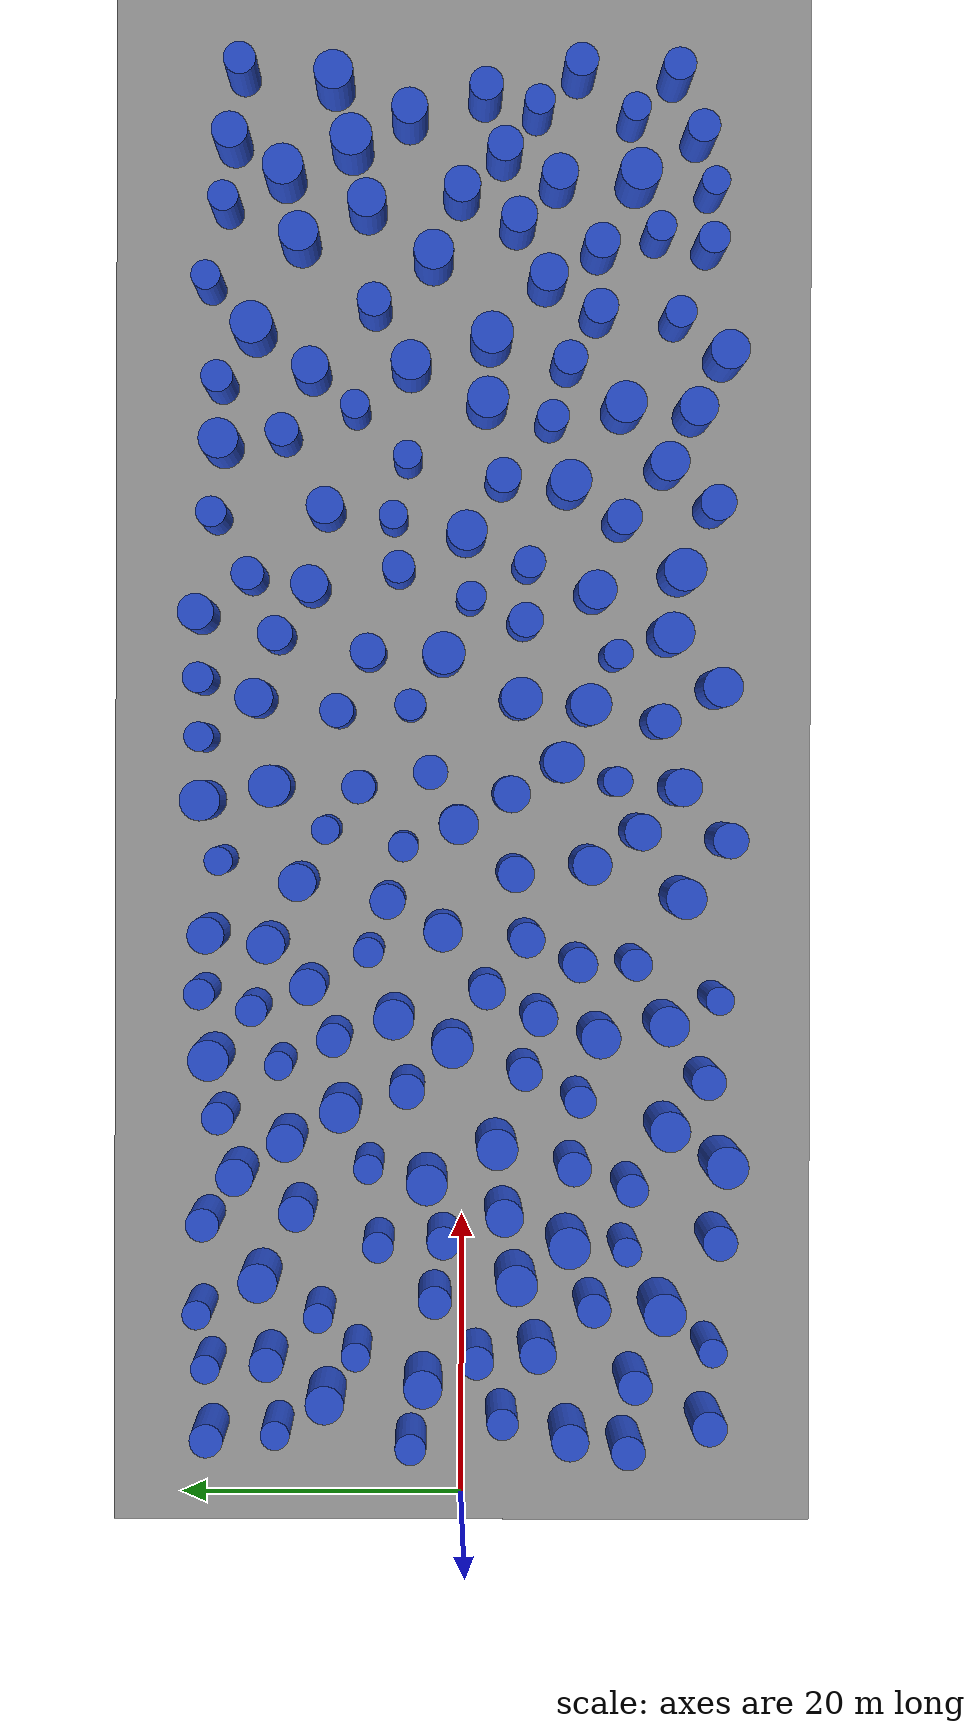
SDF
<sdf version="1.7">
 <world name="default">
  <plugin name="disable_physics" filename="libdisable_physics.so"/>
  <plugin name="gazebo_ros_state" filename="libgazebo_ros_state.so">
   <ros>
    <namespace>/plug</namespace>
    <argument>model_states:=model_states_plug</argument>
    <argument>link_states:=link_states_plug</argument>
   </ros>
   <update_rate>100.0</update_rate>
  </plugin>
  <light name="sun" type="directional">
   <pose>0 0 10 0 -0 0</pose>
   <diffuse>0.8 0.8 0.8 1</diffuse>
   <specular>0.2 0.2 0.2 1</specular>
   <attenuation>
    <range>1000</range>
    <constant>0.9</constant>
    <linear>0.01</linear>
    <quadratic>0.001</quadratic>
   </attenuation>
   <direction>-0.5 0.1 -0.9</direction>
   <spot><inner_angle>0</inner_angle><outer_angle>0</outer_angle><falloff>0</falloff></spot>
  </light>
  <gravity>0 0 -9.8</gravity>
  <magnetic_field>6e-06 2.3e-05 -4.2e-05</magnetic_field>
  <atmosphere type="adiabatic"/>
  <physics type="ode">
   <max_step_size>0.001</max_step_size>
   <real_time_factor>1</real_time_factor>
   <real_time_update_rate>1000</real_time_update_rate>
  </physics>
  <scene><ambient>0.4 0.4 0.4 1</ambient><background>0.7 0.7 0.7 1</background><shadows>1</shadows></scene>
  <audio><device>default</device></audio>
  <spherical_coordinates>
   <surface_model>EARTH_WGS84</surface_model>
   <latitude_deg>0</latitude_deg>
   <longitude_deg>0</longitude_deg>
   <elevation>0</elevation>
   <heading_deg>0</heading_deg>
  </spherical_coordinates>
  <model name="ground_plane_map">
   <static>1</static>
   <link name="link">
    <collision name="collision">
     <geometry><plane><normal>0 0 1</normal><size>110 50</size></plane></geometry>
     <surface>
      <contact><collide_without_contact>1</collide_without_contact></contact>
      <friction><ode><mu>100</mu><mu2>50</mu2></ode></friction>
     </surface>
    </collision>
    <visual name="visual">
     <cast_shadows>0</cast_shadows>
     <geometry><plane><normal>0 0 1</normal><size>110 50</size></plane></geometry>
     <material>
      <script><uri>file://media/materials/scripts/gazebo.material</uri><name>Gazebo/Grey</name></script>
     </material>
    </visual>
   </link>
   <pose>53 0 0 0 -0 0</pose>
  </model>
  <model name="0">
   <static>1</static>
   <link name="link">
    <inertial>
     <mass>2</mass>
     <inertia><ixx>6.95079</ixx><ixy>0</ixy><ixz>0</ixz><iyy>6.95079</iyy><iyz>0</iyz><izz>1.90158</izz></inertia>
    </inertial>
    <collision name="collision">
     <geometry><cylinder><length>6</length><radius>1.37898</radius></cylinder></geometry>
     <surface><contact><collide_without_contact>1</collide_without_contact></contact></surface>
    </collision>
    <visual name="visual">
     <geometry><cylinder><length>6</length><radius>1.37898</radius></cylinder></geometry>
     <material>
      <script><uri>file://media/materials/scripts/gazebo.material</uri><name>Gazebo/Blue</name></script>
     </material>
    </visual>
    <gravity>0</gravity>
   </link>
   <pose>45.2762 -8.97843 3 0 -0 0</pose>
  </model>
  <model name="1">
   <static>1</static>
   <link name="link">
    <inertial>
     <mass>2</mass>
     <inertia><ixx>6.72296</ixx><ixy>0</ixy><ixz>0</ixz><iyy>6.72296</iyy><iyz>0</iyz><izz>1.44593</izz></inertia>
    </inertial>
    <collision name="collision">
     <geometry><cylinder><length>6</length><radius>1.20247</radius></cylinder></geometry>
     <surface><contact><collide_without_contact>1</collide_without_contact></contact></surface>
    </collision>
    <visual name="visual">
     <geometry><cylinder><length>6</length><radius>1.20247</radius></cylinder></geometry>
     <material>
      <script><uri>file://media/materials/scripts/gazebo.material</uri><name>Gazebo/Blue</name></script>
     </material>
    </visual>
    <gravity>0</gravity>
   </link>
   <pose>80.6973 -7.39447 3 0 -0 0</pose>
  </model>
  <model name="2">
   <static>1</static>
   <link name="link">
    <inertial>
     <mass>2</mass>
     <inertia><ixx>6.83423</ixx><ixy>0</ixy><ixz>0</ixz><iyy>6.83423</iyy><iyz>0</iyz><izz>1.66847</izz></inertia>
    </inertial>
    <collision name="collision">
     <geometry><cylinder><length>6</length><radius>1.29169</radius></cylinder></geometry>
     <surface><contact><collide_without_contact>1</collide_without_contact></contact></surface>
    </collision>
    <visual name="visual">
     <geometry><cylinder><length>6</length><radius>1.29169</radius></cylinder></geometry>
     <material>
      <script><uri>file://media/materials/scripts/gazebo.material</uri><name>Gazebo/Blue</name></script>
     </material>
    </visual>
    <gravity>0</gravity>
   </link>
   <pose>92.757 0.175366 3 0 -0 0</pose>
  </model>
  <model name="3">
   <static>1</static>
   <link name="link">
    <inertial>
     <mass>2</mass>
     <inertia><ixx>6.94931</ixx><ixy>0</ixy><ixz>0</ixz><iyy>6.94931</iyy><iyz>0</iyz><izz>1.89861</izz></inertia>
    </inertial>
    <collision name="collision">
     <geometry><cylinder><length>6</length><radius>1.3779</radius></cylinder></geometry>
     <surface><contact><collide_without_contact>1</collide_without_contact></contact></surface>
    </collision>
    <visual name="visual">
     <geometry><cylinder><length>6</length><radius>1.3779</radius></cylinder></geometry>
     <material>
      <script><uri>file://media/materials/scripts/gazebo.material</uri><name>Gazebo/Blue</name></script>
     </material>
    </visual>
    <gravity>0</gravity>
   </link>
   <pose>64.5107 -9.29219 3 0 -0 0</pose>
  </model>
  <model name="4">
   <static>1</static>
   <link name="link">
    <inertial>
     <mass>2</mass>
     <inertia><ixx>7.11213</ixx><ixy>0</ixy><ixz>0</ixz><iyy>7.11213</iyy><iyz>0</iyz><izz>2.22425</izz></inertia>
    </inertial>
    <collision name="collision">
     <geometry><cylinder><length>6</length><radius>1.49139</radius></cylinder></geometry>
     <surface><contact><collide_without_contact>1</collide_without_contact></contact></surface>
    </collision>
    <visual name="visual">
     <geometry><cylinder><length>6</length><radius>1.49139</radius></cylinder></geometry>
     <material>
      <script><uri>file://media/materials/scripts/gazebo.material</uri><name>Gazebo/Blue</name></script>
     </material>
    </visual>
    <gravity>0</gravity>
   </link>
   <pose>83.0964 14.8871 3 0 -0 0</pose>
  </model>
  <model name="5">
   <static>1</static>
   <link name="link">
    <inertial>
     <mass>2</mass>
     <inertia><ixx>6.9315</ixx><ixy>0</ixy><ixz>0</ixz><iyy>6.9315</iyy><iyz>0</iyz><izz>1.863</izz></inertia>
    </inertial>
    <collision name="collision">
     <geometry><cylinder><length>6</length><radius>1.36492</radius></cylinder></geometry>
     <surface><contact><collide_without_contact>1</collide_without_contact></contact></surface>
    </collision>
    <visual name="visual">
     <geometry><cylinder><length>6</length><radius>1.36492</radius></cylinder></geometry>
     <material>
      <script><uri>file://media/materials/scripts/gazebo.material</uri><name>Gazebo/Blue</name></script>
     </material>
    </visual>
    <gravity>0</gravity>
   </link>
   <pose>91.7951 6.85711 3 0 -0 0</pose>
  </model>
  <model name="6">
   <static>1</static>
   <link name="link">
    <inertial>
     <mass>2</mass>
     <inertia><ixx>6.55162</ixx><ixy>0</ixy><ixz>0</ixz><iyy>6.55162</iyy><iyz>0</iyz><izz>1.10324</izz></inertia>
    </inertial>
    <collision name="collision">
     <geometry><cylinder><length>6</length><radius>1.05035</radius></cylinder></geometry>
     <surface><contact><collide_without_contact>1</collide_without_contact></contact></surface>
    </collision>
    <visual name="visual">
     <geometry><cylinder><length>6</length><radius>1.05035</radius></cylinder></geometry>
     <material>
      <script><uri>file://media/materials/scripts/gazebo.material</uri><name>Gazebo/Blue</name></script>
     </material>
    </visual>
    <gravity>0</gravity>
   </link>
   <pose>46.5555 4.20254 3 0 -0 0</pose>
  </model>
  <model name="7">
   <static>1</static>
   <link name="link">
    <inertial>
     <mass>2</mass>
     <inertia><ixx>7.10009</ixx><ixy>0</ixy><ixz>0</ixz><iyy>7.10009</iyy><iyz>0</iyz><izz>2.20019</izz></inertia>
    </inertial>
    <collision name="collision">
     <geometry><cylinder><length>6</length><radius>1.4833</radius></cylinder></geometry>
     <surface><contact><collide_without_contact>1</collide_without_contact></contact></surface>
    </collision>
    <visual name="visual">
     <geometry><cylinder><length>6</length><radius>1.4833</radius></cylinder></geometry>
     <material>
      <script><uri>file://media/materials/scripts/gazebo.material</uri><name>Gazebo/Blue</name></script>
     </material>
    </visual>
    <gravity>0</gravity>
   </link>
   <pose>50.7692 13.5287 3 0 -0 0</pose>
  </model>
  <model name="8">
   <static>1</static>
   <link name="link">
    <inertial>
     <mass>2</mass>
     <inertia><ixx>6.98352</ixx><ixy>0</ixy><ixz>0</ixz><iyy>6.98352</iyy><iyz>0</iyz><izz>1.96705</izz></inertia>
    </inertial>
    <collision name="collision">
     <geometry><cylinder><length>6</length><radius>1.40251</radius></cylinder></geometry>
     <surface><contact><collide_without_contact>1</collide_without_contact></contact></surface>
    </collision>
    <visual name="visual">
     <geometry><cylinder><length>6</length><radius>1.40251</radius></cylinder></geometry>
     <material>
      <script><uri>file://media/materials/scripts/gazebo.material</uri><name>Gazebo/Blue</name></script>
     </material>
    </visual>
    <gravity>0</gravity>
   </link>
   <pose>57.7333 -18.0752 3 0 -0 0</pose>
  </model>
  <model name="9">
   <static>1</static>
   <link name="link">
    <inertial>
     <mass>2</mass>
     <inertia><ixx>6.71929</ixx><ixy>0</ixy><ixz>0</ixz><iyy>6.71929</iyy><iyz>0</iyz><izz>1.43859</izz></inertia>
    </inertial>
    <collision name="collision">
     <geometry><cylinder><length>6</length><radius>1.19941</radius></cylinder></geometry>
     <surface><contact><collide_without_contact>1</collide_without_contact></contact></surface>
    </collision>
    <visual name="visual">
     <geometry><cylinder><length>6</length><radius>1.19941</radius></cylinder></geometry>
     <material>
      <script><uri>file://media/materials/scripts/gazebo.material</uri><name>Gazebo/Blue</name></script>
     </material>
    </visual>
    <gravity>0</gravity>
   </link>
   <pose>84.7053 6.32276 3 0 -0 0</pose>
  </model>
  <model name="10">
   <static>1</static>
   <link name="link">
    <inertial>
     <mass>2</mass>
     <inertia><ixx>6.77724</ixx><ixy>0</ixy><ixz>0</ixz><iyy>6.77724</iyy><iyz>0</iyz><izz>1.55448</izz></inertia>
    </inertial>
    <collision name="collision">
     <geometry><cylinder><length>6</length><radius>1.24679</radius></cylinder></geometry>
     <surface><contact><collide_without_contact>1</collide_without_contact></contact></surface>
    </collision>
    <visual name="visual">
     <geometry><cylinder><length>6</length><radius>1.24679</radius></cylinder></geometry>
     <material>
      <script><uri>file://media/materials/scripts/gazebo.material</uri><name>Gazebo/Blue</name></script>
     </material>
    </visual>
    <gravity>0</gravity>
   </link>
   <pose>88.8436 -9.60499 3 0 -0 0</pose>
  </model>
  <model name="11">
   <static>1</static>
   <link name="link">
    <inertial>
     <mass>2</mass>
     <inertia><ixx>7.02995</ixx><ixy>0</ixy><ixz>0</ixz><iyy>7.02995</iyy><iyz>0</iyz><izz>2.0599</izz></inertia>
    </inertial>
    <collision name="collision">
     <geometry><cylinder><length>6</length><radius>1.43524</radius></cylinder></geometry>
     <surface><contact><collide_without_contact>1</collide_without_contact></contact></surface>
    </collision>
    <visual name="visual">
     <geometry><cylinder><length>6</length><radius>1.43524</radius></cylinder></geometry>
     <material>
      <script><uri>file://media/materials/scripts/gazebo.material</uri><name>Gazebo/Blue</name></script>
     </material>
    </visual>
    <gravity>0</gravity>
   </link>
   <pose>22.9935 2.50664 3 0 -0 0</pose>
  </model>
  <model name="12">
   <static>1</static>
   <link name="link">
    <inertial>
     <mass>2</mass>
     <inertia><ixx>7.10079</ixx><ixy>0</ixy><ixz>0</ixz><iyy>7.10079</iyy><iyz>0</iyz><izz>2.20157</izz></inertia>
    </inertial>
    <collision name="collision">
     <geometry><cylinder><length>6</length><radius>1.48377</radius></cylinder></geometry>
     <surface><contact><collide_without_contact>1</collide_without_contact></contact></surface>
    </collision>
    <visual name="visual">
     <geometry><cylinder><length>6</length><radius>1.48377</radius></cylinder></geometry>
     <material>
      <script><uri>file://media/materials/scripts/gazebo.material</uri><name>Gazebo/Blue</name></script>
     </material>
    </visual>
    <gravity>0</gravity>
   </link>
   <pose>82.4183 -1.92681 3 0 -0 0</pose>
  </model>
  <model name="13">
   <static>1</static>
   <link name="link">
    <inertial>
     <mass>2</mass>
     <inertia><ixx>6.67283</ixx><ixy>0</ixy><ixz>0</ixz><iyy>6.67283</iyy><iyz>0</iyz><izz>1.34566</izz></inertia>
    </inertial>
    <collision name="collision">
     <geometry><cylinder><length>6</length><radius>1.16003</radius></cylinder></geometry>
     <surface><contact><collide_without_contact>1</collide_without_contact></contact></surface>
    </collision>
    <visual name="visual">
     <geometry><cylinder><length>6</length><radius>1.16003</radius></cylinder></geometry>
     <material>
      <script><uri>file://media/materials/scripts/gazebo.material</uri><name>Gazebo/Blue</name></script>
     </material>
    </visual>
    <gravity>0</gravity>
   </link>
   <pose>14.8128 1.93175 3 0 -0 0</pose>
  </model>
  <model name="14">
   <static>1</static>
   <link name="link">
    <inertial>
     <mass>2</mass>
     <inertia><ixx>6.81118</ixx><ixy>0</ixy><ixz>0</ixz><iyy>6.81118</iyy><iyz>0</iyz><izz>1.62236</izz></inertia>
    </inertial>
    <collision name="collision">
     <geometry><cylinder><length>6</length><radius>1.27372</radius></cylinder></geometry>
     <surface><contact><collide_without_contact>1</collide_without_contact></contact></surface>
    </collision>
    <visual name="visual">
     <geometry><cylinder><length>6</length><radius>1.27372</radius></cylinder></geometry>
     <material>
      <script><uri>file://media/materials/scripts/gazebo.material</uri><name>Gazebo/Blue</name></script>
     </material>
    </visual>
    <gravity>0</gravity>
   </link>
   <pose>98.2023 3.86457 3 0 -0 0</pose>
  </model>
  <model name="15">
   <static>1</static>
   <link name="link">
    <inertial>
     <mass>2</mass>
     <inertia><ixx>6.74725</ixx><ixy>0</ixy><ixz>0</ixz><iyy>6.74725</iyy><iyz>0</iyz><izz>1.49449</izz></inertia>
    </inertial>
    <collision name="collision">
     <geometry><cylinder><length>6</length><radius>1.22249</radius></cylinder></geometry>
     <surface><contact><collide_without_contact>1</collide_without_contact></contact></surface>
    </collision>
    <visual name="visual">
     <geometry><cylinder><length>6</length><radius>1.22249</radius></cylinder></geometry>
     <material>
      <script><uri>file://media/materials/scripts/gazebo.material</uri><name>Gazebo/Blue</name></script>
     </material>
    </visual>
    <gravity>0</gravity>
   </link>
   <pose>62.3933 -4.32254 3 0 -0 0</pose>
  </model>
  <model name="16">
   <static>1</static>
   <link name="link">
    <inertial>
     <mass>2</mass>
     <inertia><ixx>6.6557</ixx><ixy>0</ixy><ixz>0</ixz><iyy>6.6557</iyy><iyz>0</iyz><izz>1.3114</izz></inertia>
    </inertial>
    <collision name="collision">
     <geometry><cylinder><length>6</length><radius>1.14516</radius></cylinder></geometry>
     <surface><contact><collide_without_contact>1</collide_without_contact></contact></surface>
    </collision>
    <visual name="visual">
     <geometry><cylinder><length>6</length><radius>1.14516</radius></cylinder></geometry>
     <material>
      <script><uri>file://media/materials/scripts/gazebo.material</uri><name>Gazebo/Blue</name></script>
     </material>
    </visual>
    <gravity>0</gravity>
   </link>
   <pose>22.6505 -11.8133 3 0 -0 0</pose>
  </model>
  <model name="17">
   <static>1</static>
   <link name="link">
    <inertial>
     <mass>2</mass>
     <inertia><ixx>6.88223</ixx><ixy>0</ixy><ixz>0</ixz><iyy>6.88223</iyy><iyz>0</iyz><izz>1.76446</izz></inertia>
    </inertial>
    <collision name="collision">
     <geometry><cylinder><length>6</length><radius>1.32833</radius></cylinder></geometry>
     <surface><contact><collide_without_contact>1</collide_without_contact></contact></surface>
    </collision>
    <visual name="visual">
     <geometry><cylinder><length>6</length><radius>1.32833</radius></cylinder></geometry>
     <material>
      <script><uri>file://media/materials/scripts/gazebo.material</uri><name>Gazebo/Blue</name></script>
     </material>
    </visual>
    <gravity>0</gravity>
   </link>
   <pose>50.7154 -15.3173 3 0 -0 0</pose>
  </model>
  <model name="18">
   <static>1</static>
   <link name="link">
    <inertial>
     <mass>2</mass>
     <inertia><ixx>7.03448</ixx><ixy>0</ixy><ixz>0</ixz><iyy>7.03448</iyy><iyz>0</iyz><izz>2.06895</izz></inertia>
    </inertial>
    <collision name="collision">
     <geometry><cylinder><length>6</length><radius>1.43839</radius></cylinder></geometry>
     <surface><contact><collide_without_contact>1</collide_without_contact></contact></surface>
    </collision>
    <visual name="visual">
     <geometry><cylinder><length>6</length><radius>1.43839</radius></cylinder></geometry>
     <material>
      <script><uri>file://media/materials/scripts/gazebo.material</uri><name>Gazebo/Blue</name></script>
     </material>
    </visual>
    <gravity>0</gravity>
   </link>
   <pose>94.1201 12.7132 3 0 -0 0</pose>
  </model>
  <model name="19">
   <static>1</static>
   <link name="link">
    <inertial>
     <mass>2</mass>
     <inertia><ixx>7.06805</ixx><ixy>0</ixy><ixz>0</ixz><iyy>7.06805</iyy><iyz>0</iyz><izz>2.1361</izz></inertia>
    </inertial>
    <collision name="collision">
     <geometry><cylinder><length>6</length><radius>1.46154</radius></cylinder></geometry>
     <surface><contact><collide_without_contact>1</collide_without_contact></contact></surface>
    </collision>
    <visual name="visual">
     <geometry><cylinder><length>6</length><radius>1.46154</radius></cylinder></geometry>
     <material>
      <script><uri>file://media/materials/scripts/gazebo.material</uri><name>Gazebo/Blue</name></script>
     </material>
    </visual>
    <gravity>0</gravity>
   </link>
   <pose>56.9413 -4.03041 3 0 -0 0</pose>
  </model>
  <model name="20">
   <static>1</static>
   <link name="link">
    <inertial>
     <mass>2</mass>
     <inertia><ixx>6.64731</ixx><ixy>0</ixy><ixz>0</ixz><iyy>6.64731</iyy><iyz>0</iyz><izz>1.29463</izz></inertia>
    </inertial>
    <collision name="collision">
     <geometry><cylinder><length>6</length><radius>1.13782</radius></cylinder></geometry>
     <surface><contact><collide_without_contact>1</collide_without_contact></contact></surface>
    </collision>
    <visual name="visual">
     <geometry><cylinder><length>6</length><radius>1.13782</radius></cylinder></geometry>
     <material>
      <script><uri>file://media/materials/scripts/gazebo.material</uri><name>Gazebo/Blue</name></script>
     </material>
    </visual>
    <gravity>0</gravity>
   </link>
   <pose>101.496 15.7288 3 0 -0 0</pose>
  </model>
  <model name="21">
   <static>1</static>
   <link name="link">
    <inertial>
     <mass>2</mass>
     <inertia><ixx>6.54203</ixx><ixy>0</ixy><ixz>0</ixz><iyy>6.54203</iyy><iyz>0</iyz><izz>1.08407</izz></inertia>
    </inertial>
    <collision name="collision">
     <geometry><cylinder><length>6</length><radius>1.04119</radius></cylinder></geometry>
     <surface><contact><collide_without_contact>1</collide_without_contact></contact></surface>
    </collision>
    <visual name="visual">
     <geometry><cylinder><length>6</length><radius>1.04119</radius></cylinder></geometry>
     <material>
      <script><uri>file://media/materials/scripts/gazebo.material</uri><name>Gazebo/Blue</name></script>
     </material>
    </visual>
    <gravity>0</gravity>
   </link>
   <pose>64.0435 -0.514004 3 0 -0 0</pose>
  </model>
  <model name="22">
   <static>1</static>
   <link name="link">
    <inertial>
     <mass>2</mass>
     <inertia><ixx>7.01181</ixx><ixy>0</ixy><ixz>0</ixz><iyy>7.01181</iyy><iyz>0</iyz><izz>2.02362</izz></inertia>
    </inertial>
    <collision name="collision">
     <geometry><cylinder><length>6</length><radius>1.42254</radius></cylinder></geometry>
     <surface><contact><collide_without_contact>1</collide_without_contact></contact></surface>
    </collision>
    <visual name="visual">
     <geometry><cylinder><length>6</length><radius>1.42254</radius></cylinder></geometry>
     <material>
      <script><uri>file://media/materials/scripts/gazebo.material</uri><name>Gazebo/Blue</name></script>
     </material>
    </visual>
    <gravity>0</gravity>
   </link>
   <pose>28.0346 8.60096 3 0 -0 0</pose>
  </model>
  <model name="23">
   <static>1</static>
   <link name="link">
    <inertial>
     <mass>2</mass>
     <inertia><ixx>6.61631</ixx><ixy>0</ixy><ixz>0</ixz><iyy>6.61631</iyy><iyz>0</iyz><izz>1.23261</izz></inertia>
    </inertial>
    <collision name="collision">
     <geometry><cylinder><length>6</length><radius>1.11023</radius></cylinder></geometry>
     <surface><contact><collide_without_contact>1</collide_without_contact></contact></surface>
    </collision>
    <visual name="visual">
     <geometry><cylinder><length>6</length><radius>1.11023</radius></cylinder></geometry>
     <material>
      <script><uri>file://media/materials/scripts/gazebo.material</uri><name>Gazebo/Blue</name></script>
     </material>
    </visual>
    <gravity>0</gravity>
   </link>
   <pose>83.8898 -15.0889 3 0 -0 0</pose>
  </model>
  <model name="24">
   <static>1</static>
   <link name="link">
    <inertial>
     <mass>2</mass>
     <inertia><ixx>6.90968</ixx><ixy>0</ixy><ixz>0</ixz><iyy>6.90968</iyy><iyz>0</iyz><izz>1.81936</izz></inertia>
    </inertial>
    <collision name="collision">
     <geometry><cylinder><length>6</length><radius>1.34884</radius></cylinder></geometry>
     <surface><contact><collide_without_contact>1</collide_without_contact></contact></surface>
    </collision>
    <visual name="visual">
     <geometry><cylinder><length>6</length><radius>1.34884</radius></cylinder></geometry>
     <material>
      <script><uri>file://media/materials/scripts/gazebo.material</uri><name>Gazebo/Blue</name></script>
     </material>
    </visual>
    <gravity>0</gravity>
   </link>
   <pose>8.75022 2.75537 3 0 -0 0</pose>
  </model>
  <model name="25">
   <static>1</static>
   <link name="link">
    <inertial>
     <mass>2</mass>
     <inertia><ixx>6.80277</ixx><ixy>0</ixy><ixz>0</ixz><iyy>6.80277</iyy><iyz>0</iyz><izz>1.60554</izz></inertia>
    </inertial>
    <collision name="collision">
     <geometry><cylinder><length>6</length><radius>1.2671</radius></cylinder></geometry>
     <surface><contact><collide_without_contact>1</collide_without_contact></contact></surface>
    </collision>
    <visual name="visual">
     <geometry><cylinder><length>6</length><radius>1.2671</radius></cylinder></geometry>
     <material>
      <script><uri>file://media/materials/scripts/gazebo.material</uri><name>Gazebo/Blue</name></script>
     </material>
    </visual>
    <gravity>0</gravity>
   </link>
   <pose>70.6013 -17.7327 3 0 -0 0</pose>
  </model>
  <model name="26">
   <static>1</static>
   <link name="link">
    <inertial>
     <mass>2</mass>
     <inertia><ixx>6.84912</ixx><ixy>0</ixy><ixz>0</ixz><iyy>6.84912</iyy><iyz>0</iyz><izz>1.69825</izz></inertia>
    </inertial>
    <collision name="collision">
     <geometry><cylinder><length>6</length><radius>1.30317</radius></cylinder></geometry>
     <surface><contact><collide_without_contact>1</collide_without_contact></contact></surface>
    </collision>
    <visual name="visual">
     <geometry><cylinder><length>6</length><radius>1.30317</radius></cylinder></geometry>
     <material>
      <script><uri>file://media/materials/scripts/gazebo.material</uri><name>Gazebo/Blue</name></script>
     </material>
    </visual>
    <gravity>0</gravity>
   </link>
   <pose>40.3525 17.9683 3 0 -0 0</pose>
  </model>
  <model name="27">
   <static>1</static>
   <link name="link">
    <inertial>
     <mass>2</mass>
     <inertia><ixx>6.51088</ixx><ixy>0</ixy><ixz>0</ixz><iyy>6.51088</iyy><iyz>0</iyz><izz>1.02175</izz></inertia>
    </inertial>
    <collision name="collision">
     <geometry><cylinder><length>6</length><radius>1.01082</radius></cylinder></geometry>
     <surface><contact><collide_without_contact>1</collide_without_contact></contact></surface>
    </collision>
    <visual name="visual">
     <geometry><cylinder><length>6</length><radius>1.01082</radius></cylinder></geometry>
     <material>
      <script><uri>file://media/materials/scripts/gazebo.material</uri><name>Gazebo/Blue</name></script>
     </material>
    </visual>
    <gravity>0</gravity>
   </link>
   <pose>98.1711 -11.9642 3 0 -0 0</pose>
  </model>
  <model name="28">
   <static>1</static>
   <link name="link">
    <inertial>
     <mass>2</mass>
     <inertia><ixx>6.61083</ixx><ixy>0</ixy><ixz>0</ixz><iyy>6.61083</iyy><iyz>0</iyz><izz>1.22166</izz></inertia>
    </inertial>
    <collision name="collision">
     <geometry><cylinder><length>6</length><radius>1.10529</radius></cylinder></geometry>
     <surface><contact><collide_without_contact>1</collide_without_contact></contact></surface>
    </collision>
    <visual name="visual">
     <geometry><cylinder><length>6</length><radius>1.10529</radius></cylinder></geometry>
     <material>
      <script><uri>file://media/materials/scripts/gazebo.material</uri><name>Gazebo/Blue</name></script>
     </material>
    </visual>
    <gravity>0</gravity>
   </link>
   <pose>6.33318 -2.81082 3 0 -0 0</pose>
  </model>
  <model name="29">
   <static>1</static>
   <link name="link">
    <inertial>
     <mass>2</mass>
     <inertia><ixx>6.6384</ixx><ixy>0</ixy><ixz>0</ixz><iyy>6.6384</iyy><iyz>0</iyz><izz>1.27681</izz></inertia>
    </inertial>
    <collision name="collision">
     <geometry><cylinder><length>6</length><radius>1.12996</radius></cylinder></geometry>
     <surface><contact><collide_without_contact>1</collide_without_contact></contact></surface>
    </collision>
    <visual name="visual">
     <geometry><cylinder><length>6</length><radius>1.12996</radius></cylinder></geometry>
     <material>
      <script><uri>file://media/materials/scripts/gazebo.material</uri><name>Gazebo/Blue</name></script>
     </material>
    </visual>
    <gravity>0</gravity>
   </link>
   <pose>38.3677 -12.0648 3 0 -0 0</pose>
  </model>
  <model name="30">
   <static>1</static>
   <link name="link">
    <inertial>
     <mass>2</mass>
     <inertia><ixx>6.51988</ixx><ixy>0</ixy><ixz>0</ixz><iyy>6.51988</iyy><iyz>0</iyz><izz>1.03977</izz></inertia>
    </inertial>
    <collision name="collision">
     <geometry><cylinder><length>6</length><radius>1.01969</radius></cylinder></geometry>
     <surface><contact><collide_without_contact>1</collide_without_contact></contact></surface>
    </collision>
    <visual name="visual">
     <geometry><cylinder><length>6</length><radius>1.01969</radius></cylinder></geometry>
     <material>
      <script><uri>file://media/materials/scripts/gazebo.material</uri><name>Gazebo/Blue</name></script>
     </material>
    </visual>
    <gravity>0</gravity>
   </link>
   <pose>13.906 18.5337 3 0 -0 0</pose>
  </model>
  <model name="31">
   <static>1</static>
   <link name="link">
    <inertial>
     <mass>2</mass>
     <inertia><ixx>6.69535</ixx><ixy>0</ixy><ixz>0</ixz><iyy>6.69535</iyy><iyz>0</iyz><izz>1.3907</izz></inertia>
    </inertial>
    <collision name="collision">
     <geometry><cylinder><length>6</length><radius>1.17928</radius></cylinder></geometry>
     <surface><contact><collide_without_contact>1</collide_without_contact></contact></surface>
    </collision>
    <visual name="visual">
     <geometry><cylinder><length>6</length><radius>1.17928</radius></cylinder></geometry>
     <material>
      <script><uri>file://media/materials/scripts/gazebo.material</uri><name>Gazebo/Blue</name></script>
     </material>
    </visual>
    <gravity>0</gravity>
   </link>
   <pose>75.6136 12.7351 3 0 -0 0</pose>
  </model>
  <model name="32">
   <static>1</static>
   <link name="link">
    <inertial>
     <mass>2</mass>
     <inertia><ixx>6.5883</ixx><ixy>0</ixy><ixz>0</ixz><iyy>6.5883</iyy><iyz>0</iyz><izz>1.1766</izz></inertia>
    </inertial>
    <collision name="collision">
     <geometry><cylinder><length>6</length><radius>1.08471</radius></cylinder></geometry>
     <surface><contact><collide_without_contact>1</collide_without_contact></contact></surface>
    </collision>
    <visual name="visual">
     <geometry><cylinder><length>6</length><radius>1.08471</radius></cylinder></geometry>
     <material>
      <script><uri>file://media/materials/scripts/gazebo.material</uri><name>Gazebo/Blue</name></script>
     </material>
    </visual>
    <gravity>0</gravity>
   </link>
   <pose>69.8895 17.6498 3 0 -0 0</pose>
  </model>
  <model name="33">
   <static>1</static>
   <link name="link">
    <inertial>
     <mass>2</mass>
     <inertia><ixx>6.89526</ixx><ixy>0</ixy><ixz>0</ixz><iyy>6.89526</iyy><iyz>0</iyz><izz>1.79051</izz></inertia>
    </inertial>
    <collision name="collision">
     <geometry><cylinder><length>6</length><radius>1.3381</radius></cylinder></geometry>
     <surface><contact><collide_without_contact>1</collide_without_contact></contact></surface>
    </collision>
    <visual name="visual">
     <geometry><cylinder><length>6</length><radius>1.3381</radius></cylinder></geometry>
     <material>
      <script><uri>file://media/materials/scripts/gazebo.material</uri><name>Gazebo/Blue</name></script>
     </material>
    </visual>
    <gravity>0</gravity>
   </link>
   <pose>86.618 -5.88549 3 0 -0 0</pose>
  </model>
  <model name="34">
   <static>1</static>
   <link name="link">
    <inertial>
     <mass>2</mass>
     <inertia><ixx>6.84292</ixx><ixy>0</ixy><ixz>0</ixz><iyy>6.84292</iyy><iyz>0</iyz><izz>1.68583</izz></inertia>
    </inertial>
    <collision name="collision">
     <geometry><cylinder><length>6</length><radius>1.2984</radius></cylinder></geometry>
     <surface><contact><collide_without_contact>1</collide_without_contact></contact></surface>
    </collision>
    <visual name="visual">
     <geometry><cylinder><length>6</length><radius>1.2984</radius></cylinder></geometry>
     <material>
      <script><uri>file://media/materials/scripts/gazebo.material</uri><name>Gazebo/Blue</name></script>
     </material>
    </visual>
    <gravity>0</gravity>
   </link>
   <pose>50.2362 -3.36983 3 0 -0 0</pose>
  </model>
  <model name="35">
   <static>1</static>
   <link name="link">
    <inertial>
     <mass>2</mass>
     <inertia><ixx>6.78663</ixx><ixy>0</ixy><ixz>0</ixz><iyy>6.78663</iyy><iyz>0</iyz><izz>1.57327</izz></inertia>
    </inertial>
    <collision name="collision">
     <geometry><cylinder><length>6</length><radius>1.2543</radius></cylinder></geometry>
     <surface><contact><collide_without_contact>1</collide_without_contact></contact></surface>
    </collision>
    <visual name="visual">
     <geometry><cylinder><length>6</length><radius>1.2543</radius></cylinder></geometry>
     <material>
      <script><uri>file://media/materials/scripts/gazebo.material</uri><name>Gazebo/Blue</name></script>
     </material>
    </visual>
    <gravity>0</gravity>
   </link>
   <pose>34.6176 -5.35558 3 0 -0 0</pose>
  </model>
  <model name="36">
   <static>1</static>
   <link name="link">
    <inertial>
     <mass>2</mass>
     <inertia><ixx>6.63334</ixx><ixy>0</ixy><ixz>0</ixz><iyy>6.63334</iyy><iyz>0</iyz><izz>1.26667</izz></inertia>
    </inertial>
    <collision name="collision">
     <geometry><cylinder><length>6</length><radius>1.12547</radius></cylinder></geometry>
     <surface><contact><collide_without_contact>1</collide_without_contact></contact></surface>
    </collision>
    <visual name="visual">
     <geometry><cylinder><length>6</length><radius>1.12547</radius></cylinder></geometry>
     <material>
      <script><uri>file://media/materials/scripts/gazebo.material</uri><name>Gazebo/Blue</name></script>
     </material>
    </visual>
    <gravity>0</gravity>
   </link>
   <pose>76.6137 -6.194 3 0 -0 0</pose>
  </model>
  <model name="37">
   <static>1</static>
   <link name="link">
    <inertial>
     <mass>2</mass>
     <inertia><ixx>6.6503</ixx><ixy>0</ixy><ixz>0</ixz><iyy>6.6503</iyy><iyz>0</iyz><izz>1.30061</izz></inertia>
    </inertial>
    <collision name="collision">
     <geometry><cylinder><length>6</length><radius>1.14044</radius></cylinder></geometry>
     <surface><contact><collide_without_contact>1</collide_without_contact></contact></surface>
    </collision>
    <visual name="visual">
     <geometry><cylinder><length>6</length><radius>1.14044</radius></cylinder></geometry>
     <material>
      <script><uri>file://media/materials/scripts/gazebo.material</uri><name>Gazebo/Blue</name></script>
     </material>
    </visual>
    <gravity>0</gravity>
   </link>
   <pose>27.6058 17.0916 3 0 -0 0</pose>
  </model>
  <model name="38">
   <static>1</static>
   <link name="link">
    <inertial>
     <mass>2</mass>
     <inertia><ixx>6.6543</ixx><ixy>0</ixy><ixz>0</ixz><iyy>6.6543</iyy><iyz>0</iyz><izz>1.3086</izz></inertia>
    </inertial>
    <collision name="collision">
     <geometry><cylinder><length>6</length><radius>1.14394</radius></cylinder></geometry>
     <surface><contact><collide_without_contact>1</collide_without_contact></contact></surface>
    </collision>
    <visual name="visual">
     <geometry><cylinder><length>6</length><radius>1.14394</radius></cylinder></geometry>
     <material>
      <script><uri>file://media/materials/scripts/gazebo.material</uri><name>Gazebo/Blue</name></script>
     </material>
    </visual>
    <gravity>0</gravity>
   </link>
   <pose>66.0688 4.56607 3 0 -0 0</pose>
  </model>
  <model name="39">
   <static>1</static>
   <link name="link">
    <inertial>
     <mass>2</mass>
     <inertia><ixx>6.71283</ixx><ixy>0</ixy><ixz>0</ixz><iyy>6.71283</iyy><iyz>0</iyz><izz>1.42566</izz></inertia>
    </inertial>
    <collision name="collision">
     <geometry><cylinder><length>6</length><radius>1.19401</radius></cylinder></geometry>
     <surface><contact><collide_without_contact>1</collide_without_contact></contact></surface>
    </collision>
    <visual name="visual">
     <geometry><cylinder><length>6</length><radius>1.19401</radius></cylinder></geometry>
     <material>
      <script><uri>file://media/materials/scripts/gazebo.material</uri><name>Gazebo/Blue</name></script>
     </material>
    </visual>
    <gravity>0</gravity>
   </link>
   <pose>4.34279 -11.5728 3 0 -0 0</pose>
  </model>
  <model name="40">
   <static>1</static>
   <link name="link">
    <inertial>
     <mass>2</mass>
     <inertia><ixx>6.62687</ixx><ixy>0</ixy><ixz>0</ixz><iyy>6.62687</iyy><iyz>0</iyz><izz>1.25375</izz></inertia>
    </inertial>
    <collision name="collision">
     <geometry><cylinder><length>6</length><radius>1.11971</radius></cylinder></geometry>
     <surface><contact><collide_without_contact>1</collide_without_contact></contact></surface>
    </collision>
    <visual name="visual">
     <geometry><cylinder><length>6</length><radius>1.11971</radius></cylinder></geometry>
     <material>
      <script><uri>file://media/materials/scripts/gazebo.material</uri><name>Gazebo/Blue</name></script>
     </material>
    </visual>
    <gravity>0</gravity>
   </link>
   <pose>66.4322 -4.58232 3 0 -0 0</pose>
  </model>
  <model name="41">
   <static>1</static>
   <link name="link">
    <inertial>
     <mass>2</mass>
     <inertia><ixx>6.82443</ixx><ixy>0</ixy><ixz>0</ixz><iyy>6.82443</iyy><iyz>0</iyz><izz>1.64885</izz></inertia>
    </inertial>
    <collision name="collision">
     <geometry><cylinder><length>6</length><radius>1.28408</radius></cylinder></geometry>
     <surface><contact><collide_without_contact>1</collide_without_contact></contact></surface>
    </collision>
    <visual name="visual">
     <geometry><cylinder><length>6</length><radius>1.28408</radius></cylinder></geometry>
     <material>
      <script><uri>file://media/materials/scripts/gazebo.material</uri><name>Gazebo/Blue</name></script>
     </material>
    </visual>
    <gravity>0</gravity>
   </link>
   <pose>44.6605 -3.65832 3 0 -0 0</pose>
  </model>
  <model name="42">
   <static>1</static>
   <link name="link">
    <inertial>
     <mass>2</mass>
     <inertia><ixx>6.73098</ixx><ixy>0</ixy><ixz>0</ixz><iyy>6.73098</iyy><iyz>0</iyz><izz>1.46195</izz></inertia>
    </inertial>
    <collision name="collision">
     <geometry><cylinder><length>6</length><radius>1.20911</radius></cylinder></geometry>
     <surface><contact><collide_without_contact>1</collide_without_contact></contact></surface>
    </collision>
    <visual name="visual">
     <geometry><cylinder><length>6</length><radius>1.20911</radius></cylinder></geometry>
     <material>
      <script><uri>file://media/materials/scripts/gazebo.material</uri><name>Gazebo/Blue</name></script>
     </material>
    </visual>
    <gravity>0</gravity>
   </link>
   <pose>51.7574 2.30771 3 0 -0 0</pose>
  </model>
  <model name="43">
   <static>1</static>
   <link name="link">
    <inertial>
     <mass>2</mass>
     <inertia><ixx>7.03959</ixx><ixy>0</ixy><ixz>0</ixz><iyy>7.03959</iyy><iyz>0</iyz><izz>2.07918</izz></inertia>
    </inertial>
    <collision name="collision">
     <geometry><cylinder><length>6</length><radius>1.44194</radius></cylinder></geometry>
     <surface><contact><collide_without_contact>1</collide_without_contact></contact></surface>
    </collision>
    <visual name="visual">
     <geometry><cylinder><length>6</length><radius>1.44194</radius></cylinder></geometry>
     <material>
      <script><uri>file://media/materials/scripts/gazebo.material</uri><name>Gazebo/Blue</name></script>
     </material>
    </visual>
    <gravity>0</gravity>
   </link>
   <pose>52.4739 -6.97567 3 0 -0 0</pose>
  </model>
  <model name="44">
   <static>1</static>
   <link name="link">
    <inertial>
     <mass>2</mass>
     <inertia><ixx>6.98634</ixx><ixy>0</ixy><ixz>0</ixz><iyy>6.98634</iyy><iyz>0</iyz><izz>1.97268</izz></inertia>
    </inertial>
    <collision name="collision">
     <geometry><cylinder><length>6</length><radius>1.40452</radius></cylinder></geometry>
     <surface><contact><collide_without_contact>1</collide_without_contact></contact></surface>
    </collision>
    <visual name="visual">
     <geometry><cylinder><length>6</length><radius>1.40452</radius></cylinder></geometry>
     <material>
      <script><uri>file://media/materials/scripts/gazebo.material</uri><name>Gazebo/Blue</name></script>
     </material>
    </visual>
    <gravity>0</gravity>
   </link>
   <pose>89.4482 11.619 3 0 -0 0</pose>
  </model>
  <model name="45">
   <static>1</static>
   <link name="link">
    <inertial>
     <mass>2</mass>
     <inertia><ixx>7.12457</ixx><ixy>0</ixy><ixz>0</ixz><iyy>7.12457</iyy><iyz>0</iyz><izz>2.24913</izz></inertia>
    </inertial>
    <collision name="collision">
     <geometry><cylinder><length>6</length><radius>1.49971</radius></cylinder></geometry>
     <surface><contact><collide_without_contact>1</collide_without_contact></contact></surface>
    </collision>
    <visual name="visual">
     <geometry><cylinder><length>6</length><radius>1.49971</radius></cylinder></geometry>
     <material>
      <script><uri>file://media/materials/scripts/gazebo.material</uri><name>Gazebo/Blue</name></script>
     </material>
    </visual>
    <gravity>0</gravity>
   </link>
   <pose>65.9097 -15.412 3 0 -0 0</pose>
  </model>
  <model name="46">
   <static>1</static>
   <link name="link">
    <inertial>
     <mass>2</mass>
     <inertia><ixx>7.11514</ixx><ixy>0</ixy><ixz>0</ixz><iyy>7.11514</iyy><iyz>0</iyz><izz>2.23028</izz></inertia>
    </inertial>
    <collision name="collision">
     <geometry><cylinder><length>6</length><radius>1.49341</radius></cylinder></geometry>
     <surface><contact><collide_without_contact>1</collide_without_contact></contact></surface>
    </collision>
    <visual name="visual">
     <geometry><cylinder><length>6</length><radius>1.49341</radius></cylinder></geometry>
     <material>
      <script><uri>file://media/materials/scripts/gazebo.material</uri><name>Gazebo/Blue</name></script>
     </material>
    </visual>
    <gravity>0</gravity>
   </link>
   <pose>13.9798 -14.1056 3 0 -0 0</pose>
  </model>
  <model name="47">
   <static>1</static>
   <link name="link">
    <inertial>
     <mass>2</mass>
     <inertia><ixx>7.03224</ixx><ixy>0</ixy><ixz>0</ixz><iyy>7.03224</iyy><iyz>0</iyz><izz>2.06447</izz></inertia>
    </inertial>
    <collision name="collision">
     <geometry><cylinder><length>6</length><radius>1.43683</radius></cylinder></geometry>
     <surface><contact><collide_without_contact>1</collide_without_contact></contact></surface>
    </collision>
    <visual name="visual">
     <geometry><cylinder><length>6</length><radius>1.43683</radius></cylinder></geometry>
     <material>
      <script><uri>file://media/materials/scripts/gazebo.material</uri><name>Gazebo/Blue</name></script>
     </material>
    </visual>
    <gravity>0</gravity>
   </link>
   <pose>31.6305 17.7655 3 0 -0 0</pose>
  </model>
  <model name="48">
   <static>1</static>
   <link name="link">
    <inertial>
     <mass>2</mass>
     <inertia><ixx>7.01812</ixx><ixy>0</ixy><ixz>0</ixz><iyy>7.01812</iyy><iyz>0</iyz><izz>2.03624</izz></inertia>
    </inertial>
    <collision name="collision">
     <geometry><cylinder><length>6</length><radius>1.42697</radius></cylinder></geometry>
     <surface><contact><collide_without_contact>1</collide_without_contact></contact></surface>
    </collision>
    <visual name="visual">
     <geometry><cylinder><length>6</length><radius>1.42697</radius></cylinder></geometry>
     <material>
      <script><uri>file://media/materials/scripts/gazebo.material</uri><name>Gazebo/Blue</name></script>
     </material>
    </visual>
    <gravity>0</gravity>
   </link>
   <pose>42.9644 -15.5514 3 0 -0 0</pose>
  </model>
  <model name="49">
   <static>1</static>
   <link name="link">
    <inertial>
     <mass>2</mass>
     <inertia><ixx>6.75214</ixx><ixy>0</ixy><ixz>0</ixz><iyy>6.75214</iyy><iyz>0</iyz><izz>1.50428</izz></inertia>
    </inertial>
    <collision name="collision">
     <geometry><cylinder><length>6</length><radius>1.22649</radius></cylinder></geometry>
     <surface><contact><collide_without_contact>1</collide_without_contact></contact></surface>
    </collision>
    <visual name="visual">
     <geometry><cylinder><length>6</length><radius>1.22649</radius></cylinder></geometry>
     <material>
      <script><uri>file://media/materials/scripts/gazebo.material</uri><name>Gazebo/Blue</name></script>
     </material>
    </visual>
    <gravity>0</gravity>
   </link>
   <pose>6.03836 -17.2467 3 0 -0 0</pose>
  </model>
  <model name="50">
   <static>1</static>
   <link name="link">
    <inertial>
     <mass>2</mass>
     <inertia><ixx>6.81815</ixx><ixy>0</ixy><ixz>0</ixz><iyy>6.81815</iyy><iyz>0</iyz><izz>1.6363</izz></inertia>
    </inertial>
    <collision name="collision">
     <geometry><cylinder><length>6</length><radius>1.27918</radius></cylinder></geometry>
     <surface><contact><collide_without_contact>1</collide_without_contact></contact></surface>
    </collision>
    <visual name="visual">
     <geometry><cylinder><length>6</length><radius>1.27918</radius></cylinder></geometry>
     <material>
      <script><uri>file://media/materials/scripts/gazebo.material</uri><name>Gazebo/Blue</name></script>
     </material>
    </visual>
    <gravity>0</gravity>
   </link>
   <pose>96.5079 16.4159 3 0 -0 0</pose>
  </model>
  <model name="51">
   <static>1</static>
   <link name="link">
    <inertial>
     <mass>2</mass>
     <inertia><ixx>6.52122</ixx><ixy>0</ixy><ixz>0</ixz><iyy>6.52122</iyy><iyz>0</iyz><izz>1.04245</izz></inertia>
    </inertial>
    <collision name="collision">
     <geometry><cylinder><length>6</length><radius>1.021</radius></cylinder></geometry>
     <surface><contact><collide_without_contact>1</collide_without_contact></contact></surface>
    </collision>
    <visual name="visual">
     <geometry><cylinder><length>6</length><radius>1.021</radius></cylinder></geometry>
     <material>
      <script><uri>file://media/materials/scripts/gazebo.material</uri><name>Gazebo/Blue</name></script>
     </material>
    </visual>
    <gravity>0</gravity>
   </link>
   <pose>77.4047 7.64189 3 0 -0 0</pose>
  </model>
  <model name="52">
   <static>1</static>
   <link name="link">
    <inertial>
     <mass>2</mass>
     <inertia><ixx>6.91961</ixx><ixy>0</ixy><ixz>0</ixz><iyy>6.91961</iyy><iyz>0</iyz><izz>1.83922</izz></inertia>
    </inertial>
    <collision name="collision">
     <geometry><cylinder><length>6</length><radius>1.35618</radius></cylinder></geometry>
     <surface><contact><collide_without_contact>1</collide_without_contact></contact></surface>
    </collision>
    <visual name="visual">
     <geometry><cylinder><length>6</length><radius>1.35618</radius></cylinder></geometry>
     <material>
      <script><uri>file://media/materials/scripts/gazebo.material</uri><name>Gazebo/Blue</name></script>
     </material>
    </visual>
    <gravity>0</gravity>
   </link>
   <pose>40.5909 1.41427 3 0 -0 0</pose>
  </model>
  <model name="53">
   <static>1</static>
   <link name="link">
    <inertial>
     <mass>2</mass>
     <inertia><ixx>6.83665</ixx><ixy>0</ixy><ixz>0</ixz><iyy>6.83665</iyy><iyz>0</iyz><izz>1.6733</izz></inertia>
    </inertial>
    <collision name="collision">
     <geometry><cylinder><length>6</length><radius>1.29356</radius></cylinder></geometry>
     <surface><contact><collide_without_contact>1</collide_without_contact></contact></surface>
    </collision>
    <visual name="visual">
     <geometry><cylinder><length>6</length><radius>1.29356</radius></cylinder></geometry>
     <material>
      <script><uri>file://media/materials/scripts/gazebo.material</uri><name>Gazebo/Blue</name></script>
     </material>
    </visual>
    <gravity>0</gravity>
   </link>
   <pose>36.7718 10.8356 3 0 -0 0</pose>
  </model>
  <model name="54">
   <static>1</static>
   <link name="link">
    <inertial>
     <mass>2</mass>
     <inertia><ixx>6.68343</ixx><ixy>0</ixy><ixz>0</ixz><iyy>6.68343</iyy><iyz>0</iyz><izz>1.36686</izz></inertia>
    </inertial>
    <collision name="collision">
     <geometry><cylinder><length>6</length><radius>1.16913</radius></cylinder></geometry>
     <surface><contact><collide_without_contact>1</collide_without_contact></contact></surface>
    </collision>
    <visual name="visual">
     <geometry><cylinder><length>6</length><radius>1.16913</radius></cylinder></geometry>
     <material>
      <script><uri>file://media/materials/scripts/gazebo.material</uri><name>Gazebo/Blue</name></script>
     </material>
    </visual>
    <gravity>0</gravity>
   </link>
   <pose>20.172 18.1497 3 0 -0 0</pose>
  </model>
  <model name="55">
   <static>1</static>
   <link name="link">
    <inertial>
     <mass>2</mass>
     <inertia><ixx>6.71688</ixx><ixy>0</ixy><ixz>0</ixz><iyy>6.71688</iyy><iyz>0</iyz><izz>1.43376</izz></inertia>
    </inertial>
    <collision name="collision">
     <geometry><cylinder><length>6</length><radius>1.1974</radius></cylinder></geometry>
     <surface><contact><collide_without_contact>1</collide_without_contact></contact></surface>
    </collision>
    <visual name="visual">
     <geometry><cylinder><length>6</length><radius>1.1974</radius></cylinder></geometry>
     <material>
      <script><uri>file://media/materials/scripts/gazebo.material</uri><name>Gazebo/Blue</name></script>
     </material>
    </visual>
    <gravity>0</gravity>
   </link>
   <pose>8.90747 -12.0492 3 0 -0 0</pose>
  </model>
  <model name="56">
   <static>1</static>
   <link name="link">
    <inertial>
     <mass>2</mass>
     <inertia><ixx>6.53606</ixx><ixy>0</ixy><ixz>0</ixz><iyy>6.53606</iyy><iyz>0</iyz><izz>1.07212</izz></inertia>
    </inertial>
    <collision name="collision">
     <geometry><cylinder><length>6</length><radius>1.03543</radius></cylinder></geometry>
     <surface><contact><collide_without_contact>1</collide_without_contact></contact></surface>
    </collision>
    <visual name="visual">
     <geometry><cylinder><length>6</length><radius>1.03543</radius></cylinder></geometry>
     <material>
      <script><uri>file://media/materials/scripts/gazebo.material</uri><name>Gazebo/Blue</name></script>
     </material>
    </visual>
    <gravity>0</gravity>
   </link>
   <pose>86.379 18.063 3 0 -0 0</pose>
  </model>
  <model name="57">
   <static>1</static>
   <link name="link">
    <inertial>
     <mass>2</mass>
     <inertia><ixx>6.76823</ixx><ixy>0</ixy><ixz>0</ixz><iyy>6.76823</iyy><iyz>0</iyz><izz>1.53647</izz></inertia>
    </inertial>
    <collision name="collision">
     <geometry><cylinder><length>6</length><radius>1.23954</radius></cylinder></geometry>
     <surface><contact><collide_without_contact>1</collide_without_contact></contact></surface>
    </collision>
    <visual name="visual">
     <geometry><cylinder><length>6</length><radius>1.23954</radius></cylinder></geometry>
     <material>
      <script><uri>file://media/materials/scripts/gazebo.material</uri><name>Gazebo/Blue</name></script>
     </material>
    </visual>
    <gravity>0</gravity>
   </link>
   <pose>72.4647 -2.75646 3 0 -0 0</pose>
  </model>
  <model name="58">
   <static>1</static>
   <link name="link">
    <inertial>
     <mass>2</mass>
     <inertia><ixx>6.93486</ixx><ixy>0</ixy><ixz>0</ixz><iyy>6.93486</iyy><iyz>0</iyz><izz>1.86972</izz></inertia>
    </inertial>
    <collision name="collision">
     <geometry><cylinder><length>6</length><radius>1.36738</radius></cylinder></geometry>
     <surface><contact><collide_without_contact>1</collide_without_contact></contact></surface>
    </collision>
    <visual name="visual">
     <geometry><cylinder><length>6</length><radius>1.36738</radius></cylinder></geometry>
     <material>
      <script><uri>file://media/materials/scripts/gazebo.material</uri><name>Gazebo/Blue</name></script>
     </material>
    </visual>
    <gravity>0</gravity>
   </link>
   <pose>77.3036 -16.3536 3 0 -0 0</pose>
  </model>
  <model name="59">
   <static>1</static>
   <link name="link">
    <inertial>
     <mass>2</mass>
     <inertia><ixx>6.71629</ixx><ixy>0</ixy><ixz>0</ixz><iyy>6.71629</iyy><iyz>0</iyz><izz>1.43258</izz></inertia>
    </inertial>
    <collision name="collision">
     <geometry><cylinder><length>6</length><radius>1.1969</radius></cylinder></geometry>
     <surface><contact><collide_without_contact>1</collide_without_contact></contact></surface>
    </collision>
    <visual name="visual">
     <geometry><cylinder><length>6</length><radius>1.1969</radius></cylinder></geometry>
     <material>
      <script><uri>file://media/materials/scripts/gazebo.material</uri><name>Gazebo/Blue</name></script>
     </material>
    </visual>
    <gravity>0</gravity>
   </link>
   <pose>10.4298 13.6728 3 0 -0 0</pose>
  </model>
  <model name="60">
   <static>1</static>
   <link name="link">
    <inertial>
     <mass>2</mass>
     <inertia><ixx>7.05343</ixx><ixy>0</ixy><ixz>0</ixz><iyy>7.05343</iyy><iyz>0</iyz><izz>2.10687</izz></inertia>
    </inertial>
    <collision name="collision">
     <geometry><cylinder><length>6</length><radius>1.45151</radius></cylinder></geometry>
     <surface><contact><collide_without_contact>1</collide_without_contact></contact></surface>
    </collision>
    <visual name="visual">
     <geometry><cylinder><length>6</length><radius>1.45151</radius></cylinder></geometry>
     <material>
      <script><uri>file://media/materials/scripts/gazebo.material</uri><name>Gazebo/Blue</name></script>
     </material>
    </visual>
    <gravity>0</gravity>
   </link>
   <pose>15.9973 -3.78561 3 0 -0 0</pose>
  </model>
  <model name="61">
   <static>1</static>
   <link name="link">
    <inertial>
     <mass>2</mass>
     <inertia><ixx>6.52127</ixx><ixy>0</ixy><ixz>0</ixz><iyy>6.52127</iyy><iyz>0</iyz><izz>1.04254</izz></inertia>
    </inertial>
    <collision name="collision">
     <geometry><cylinder><length>6</length><radius>1.02105</radius></cylinder></geometry>
     <surface><contact><collide_without_contact>1</collide_without_contact></contact></surface>
    </collision>
    <visual name="visual">
     <geometry><cylinder><length>6</length><radius>1.02105</radius></cylinder></geometry>
     <material>
      <script><uri>file://media/materials/scripts/gazebo.material</uri><name>Gazebo/Blue</name></script>
     </material>
    </visual>
    <gravity>0</gravity>
   </link>
   <pose>18.3576 -11.4644 3 0 -0 0</pose>
  </model>
  <model name="62">
   <static>1</static>
   <link name="link">
    <inertial>
     <mass>2</mass>
     <inertia><ixx>6.81051</ixx><ixy>0</ixy><ixz>0</ixz><iyy>6.81051</iyy><iyz>0</iyz><izz>1.62103</izz></inertia>
    </inertial>
    <collision name="collision">
     <geometry><cylinder><length>6</length><radius>1.2732</radius></cylinder></geometry>
     <surface><contact><collide_without_contact>1</collide_without_contact></contact></surface>
    </collision>
    <visual name="visual">
     <geometry><cylinder><length>6</length><radius>1.2732</radius></cylinder></geometry>
     <material>
      <script><uri>file://media/materials/scripts/gazebo.material</uri><name>Gazebo/Blue</name></script>
     </material>
    </visual>
    <gravity>0</gravity>
   </link>
   <pose>93.6427 -6.6495 3 0 -0 0</pose>
  </model>
  <model name="63">
   <static>1</static>
   <link name="link">
    <inertial>
     <mass>2</mass>
     <inertia><ixx>6.7804</ixx><ixy>0</ixy><ixz>0</ixz><iyy>6.7804</iyy><iyz>0</iyz><izz>1.56081</izz></inertia>
    </inertial>
    <collision name="collision">
     <geometry><cylinder><length>6</length><radius>1.24932</radius></cylinder></geometry>
     <surface><contact><collide_without_contact>1</collide_without_contact></contact></surface>
    </collision>
    <visual name="visual">
     <geometry><cylinder><length>6</length><radius>1.24932</radius></cylinder></geometry>
     <material>
      <script><uri>file://media/materials/scripts/gazebo.material</uri><name>Gazebo/Blue</name></script>
     </material>
    </visual>
    <gravity>0</gravity>
   </link>
   <pose>69.5819 -11.1757 3 0 -0 0</pose>
  </model>
  <model name="64">
   <static>1</static>
   <link name="link">
    <inertial>
     <mass>2</mass>
     <inertia><ixx>6.61537</ixx><ixy>0</ixy><ixz>0</ixz><iyy>6.61537</iyy><iyz>0</iyz><izz>1.23074</izz></inertia>
    </inertial>
    <collision name="collision">
     <geometry><cylinder><length>6</length><radius>1.10939</radius></cylinder></geometry>
     <surface><contact><collide_without_contact>1</collide_without_contact></contact></surface>
    </collision>
    <visual name="visual">
     <geometry><cylinder><length>6</length><radius>1.10939</radius></cylinder></geometry>
     <material>
      <script><uri>file://media/materials/scripts/gazebo.material</uri><name>Gazebo/Blue</name></script>
     </material>
    </visual>
    <gravity>0</gravity>
   </link>
   <pose>89.071 -17.4014 3 0 -0 0</pose>
  </model>
  <model name="65">
   <static>1</static>
   <link name="link">
    <inertial>
     <mass>2</mass>
     <inertia><ixx>6.52052</ixx><ixy>0</ixy><ixz>0</ixz><iyy>6.52052</iyy><iyz>0</iyz><izz>1.04104</izz></inertia>
    </inertial>
    <collision name="collision">
     <geometry><cylinder><length>6</length><radius>1.02032</radius></cylinder></geometry>
     <surface><contact><collide_without_contact>1</collide_without_contact></contact></surface>
    </collision>
    <visual name="visual">
     <geometry><cylinder><length>6</length><radius>1.02032</radius></cylinder></geometry>
     <material>
      <script><uri>file://media/materials/scripts/gazebo.material</uri><name>Gazebo/Blue</name></script>
     </material>
    </visual>
    <gravity>0</gravity>
   </link>
   <pose>5.51764 13.0563 3 0 -0 0</pose>
  </model>
  <model name="66">
   <static>1</static>
   <link name="link">
    <inertial>
     <mass>2</mass>
     <inertia><ixx>6.58357</ixx><ixy>0</ixy><ixz>0</ixz><iyy>6.58357</iyy><iyz>0</iyz><izz>1.16715</izz></inertia>
    </inertial>
    <collision name="collision">
     <geometry><cylinder><length>6</length><radius>1.08035</radius></cylinder></geometry>
     <surface><contact><collide_without_contact>1</collide_without_contact></contact></surface>
    </collision>
    <visual name="visual">
     <geometry><cylinder><length>6</length><radius>1.08035</radius></cylinder></geometry>
     <material>
      <script><uri>file://media/materials/scripts/gazebo.material</uri><name>Gazebo/Blue</name></script>
     </material>
    </visual>
    <gravity>0</gravity>
   </link>
   <pose>18.6407 5.9061 3 0 -0 0</pose>
  </model>
  <model name="67">
   <static>1</static>
   <link name="link">
    <inertial>
     <mass>2</mass>
     <inertia><ixx>6.78438</ixx><ixy>0</ixy><ixz>0</ixz><iyy>6.78438</iyy><iyz>0</iyz><izz>1.56876</izz></inertia>
    </inertial>
    <collision name="collision">
     <geometry><cylinder><length>6</length><radius>1.2525</radius></cylinder></geometry>
     <surface><contact><collide_without_contact>1</collide_without_contact></contact></surface>
    </collision>
    <visual name="visual">
     <geometry><cylinder><length>6</length><radius>1.2525</radius></cylinder></geometry>
     <material>
      <script><uri>file://media/materials/scripts/gazebo.material</uri><name>Gazebo/Blue</name></script>
     </material>
    </visual>
    <gravity>0</gravity>
   </link>
   <pose>60.2022 6.69553 3 0 -0 0</pose>
  </model>
  <model name="68">
   <static>1</static>
   <link name="link">
    <inertial>
     <mass>2</mass>
     <inertia><ixx>6.95071</ixx><ixy>0</ixy><ixz>0</ixz><iyy>6.95071</iyy><iyz>0</iyz><izz>1.90143</izz></inertia>
    </inertial>
    <collision name="collision">
     <geometry><cylinder><length>6</length><radius>1.37892</radius></cylinder></geometry>
     <surface><contact><collide_without_contact>1</collide_without_contact></contact></surface>
    </collision>
    <visual name="visual">
     <geometry><cylinder><length>6</length><radius>1.37892</radius></cylinder></geometry>
     <material>
      <script><uri>file://media/materials/scripts/gazebo.material</uri><name>Gazebo/Blue</name></script>
     </material>
    </visual>
    <gravity>0</gravity>
   </link>
   <pose>100.7 9.19752 3 0 -0 0</pose>
  </model>
  <model name="69">
   <static>1</static>
   <link name="link">
    <inertial>
     <mass>2</mass>
     <inertia><ixx>6.60836</ixx><ixy>0</ixy><ixz>0</ixz><iyy>6.60836</iyy><iyz>0</iyz><izz>1.21672</izz></inertia>
    </inertial>
    <collision name="collision">
     <geometry><cylinder><length>6</length><radius>1.10305</radius></cylinder></geometry>
     <surface><contact><collide_without_contact>1</collide_without_contact></contact></surface>
    </collision>
    <visual name="visual">
     <geometry><cylinder><length>6</length><radius>1.10305</radius></cylinder></geometry>
     <material>
      <script><uri>file://media/materials/scripts/gazebo.material</uri><name>Gazebo/Blue</name></script>
     </material>
    </visual>
    <gravity>0</gravity>
   </link>
   <pose>56.4635 3.72702 3 0 -0 0</pose>
  </model>
  <model name="70">
   <static>1</static>
   <link name="link">
    <inertial>
     <mass>2</mass>
     <inertia><ixx>6.77017</ixx><ixy>0</ixy><ixz>0</ixz><iyy>6.77017</iyy><iyz>0</iyz><izz>1.54035</izz></inertia>
    </inertial>
    <collision name="collision">
     <geometry><cylinder><length>6</length><radius>1.24111</radius></cylinder></geometry>
     <surface><contact><collide_without_contact>1</collide_without_contact></contact></surface>
    </collision>
    <visual name="visual">
     <geometry><cylinder><length>6</length><radius>1.24111</radius></cylinder></geometry>
     <material>
      <script><uri>file://media/materials/scripts/gazebo.material</uri><name>Gazebo/Blue</name></script>
     </material>
    </visual>
    <gravity>0</gravity>
   </link>
   <pose>61.4244 13.1806 3 0 -0 0</pose>
  </model>
  <model name="71">
   <static>1</static>
   <link name="link">
    <inertial>
     <mass>2</mass>
     <inertia><ixx>6.88245</ixx><ixy>0</ixy><ixz>0</ixz><iyy>6.88245</iyy><iyz>0</iyz><izz>1.76489</izz></inertia>
    </inertial>
    <collision name="collision">
     <geometry><cylinder><length>6</length><radius>1.32849</radius></cylinder></geometry>
     <surface><contact><collide_without_contact>1</collide_without_contact></contact></surface>
    </collision>
    <visual name="visual">
     <geometry><cylinder><length>6</length><radius>1.32849</radius></cylinder></geometry>
     <material>
      <script><uri>file://media/materials/scripts/gazebo.material</uri><name>Gazebo/Blue</name></script>
     </material>
    </visual>
    <gravity>0</gravity>
   </link>
   <pose>44.0516 11.5777 3 0 -0 0</pose>
  </model>
  <model name="72">
   <static>1</static>
   <link name="link">
    <inertial>
     <mass>2</mass>
     <inertia><ixx>6.87185</ixx><ixy>0</ixy><ixz>0</ixz><iyy>6.87185</iyy><iyz>0</iyz><izz>1.7437</izz></inertia>
    </inertial>
    <collision name="collision">
     <geometry><cylinder><length>6</length><radius>1.32049</radius></cylinder></geometry>
     <surface><contact><collide_without_contact>1</collide_without_contact></contact></surface>
    </collision>
    <visual name="visual">
     <geometry><cylinder><length>6</length><radius>1.32049</radius></cylinder></geometry>
     <material>
      <script><uri>file://media/materials/scripts/gazebo.material</uri><name>Gazebo/Blue</name></script>
     </material>
    </visual>
    <gravity>0</gravity>
   </link>
   <pose>64.8814 10.7806 3 0 -0 0</pose>
  </model>
  <model name="73">
   <static>1</static>
   <link name="link">
    <inertial>
     <mass>2</mass>
     <inertia><ixx>7.05981</ixx><ixy>0</ixy><ixz>0</ixz><iyy>7.05981</iyy><iyz>0</iyz><izz>2.11962</izz></inertia>
    </inertial>
    <collision name="collision">
     <geometry><cylinder><length>6</length><radius>1.45589</radius></cylinder></geometry>
     <surface><contact><collide_without_contact>1</collide_without_contact></contact></surface>
    </collision>
    <visual name="visual">
     <geometry><cylinder><length>6</length><radius>1.45589</radius></cylinder></geometry>
     <material>
      <script><uri>file://media/materials/scripts/gazebo.material</uri><name>Gazebo/Blue</name></script>
     </material>
    </visual>
    <gravity>0</gravity>
   </link>
   <pose>77.9144 -1.65153 3 0 -0 0</pose>
  </model>
  <model name="74">
   <static>1</static>
   <link name="link">
    <inertial>
     <mass>2</mass>
     <inertia><ixx>6.53838</ixx><ixy>0</ixy><ixz>0</ixz><iyy>6.53838</iyy><iyz>0</iyz><izz>1.07676</izz></inertia>
    </inertial>
    <collision name="collision">
     <geometry><cylinder><length>6</length><radius>1.03767</radius></cylinder></geometry>
     <surface><contact><collide_without_contact>1</collide_without_contact></contact></surface>
    </collision>
    <visual name="visual">
     <geometry><cylinder><length>6</length><radius>1.03767</radius></cylinder></geometry>
     <material>
      <script><uri>file://media/materials/scripts/gazebo.material</uri><name>Gazebo/Blue</name></script>
     </material>
    </visual>
    <gravity>0</gravity>
   </link>
   <pose>60.0307 -10.7714 3 0 -0 0</pose>
  </model>
  <model name="75">
   <static>1</static>
   <link name="link">
    <inertial>
     <mass>2</mass>
     <inertia><ixx>6.99362</ixx><ixy>0</ixy><ixz>0</ixz><iyy>6.99362</iyy><iyz>0</iyz><izz>1.98725</izz></inertia>
    </inertial>
    <collision name="collision">
     <geometry><cylinder><length>6</length><radius>1.4097</radius></cylinder></geometry>
     <surface><contact><collide_without_contact>1</collide_without_contact></contact></surface>
    </collision>
    <visual name="visual">
     <geometry><cylinder><length>6</length><radius>1.4097</radius></cylinder></geometry>
     <material>
      <script><uri>file://media/materials/scripts/gazebo.material</uri><name>Gazebo/Blue</name></script>
     </material>
    </visual>
    <gravity>0</gravity>
   </link>
   <pose>34.0801 -14.3724 3 0 -0 0</pose>
  </model>
  <model name="76">
   <static>1</static>
   <link name="link">
    <inertial>
     <mass>2</mass>
     <inertia><ixx>6.82305</ixx><ixy>0</ixy><ixz>0</ixz><iyy>6.82305</iyy><iyz>0</iyz><izz>1.64611</izz></inertia>
    </inertial>
    <collision name="collision">
     <geometry><cylinder><length>6</length><radius>1.28301</radius></cylinder></geometry>
     <surface><contact><collide_without_contact>1</collide_without_contact></contact></surface>
    </collision>
    <visual name="visual">
     <geometry><cylinder><length>6</length><radius>1.28301</radius></cylinder></geometry>
     <material>
      <script><uri>file://media/materials/scripts/gazebo.material</uri><name>Gazebo/Blue</name></script>
     </material>
    </visual>
    <gravity>0</gravity>
   </link>
   <pose>11.1355 -5.26871 3 0 -0 0</pose>
  </model>
  <model name="77">
   <static>1</static>
   <link name="link">
    <inertial>
     <mass>2</mass>
     <inertia><ixx>6.68907</ixx><ixy>0</ixy><ixz>0</ixz><iyy>6.68907</iyy><iyz>0</iyz><izz>1.37813</izz></inertia>
    </inertial>
    <collision name="collision">
     <geometry><cylinder><length>6</length><radius>1.17394</radius></cylinder></geometry>
     <surface><contact><collide_without_contact>1</collide_without_contact></contact></surface>
    </collision>
    <visual name="visual">
     <geometry><cylinder><length>6</length><radius>1.17394</radius></cylinder></geometry>
     <material>
      <script><uri>file://media/materials/scripts/gazebo.material</uri><name>Gazebo/Blue</name></script>
     </material>
    </visual>
    <gravity>0</gravity>
   </link>
   <pose>5.14697 17.8593 3 0 -0 0</pose>
  </model>
  <model name="78">
   <static>1</static>
   <link name="link">
    <inertial>
     <mass>2</mass>
     <inertia><ixx>6.53588</ixx><ixy>0</ixy><ixz>0</ixz><iyy>6.53588</iyy><iyz>0</iyz><izz>1.07176</izz></inertia>
    </inertial>
    <collision name="collision">
     <geometry><cylinder><length>6</length><radius>1.03526</radius></cylinder></geometry>
     <surface><contact><collide_without_contact>1</collide_without_contact></contact></surface>
    </collision>
    <visual name="visual">
     <geometry><cylinder><length>6</length><radius>1.03526</radius></cylinder></geometry>
     <material>
      <script><uri>file://media/materials/scripts/gazebo.material</uri><name>Gazebo/Blue</name></script>
     </material>
    </visual>
    <gravity>0</gravity>
   </link>
   <pose>24.0903 6.59059 3 0 -0 0</pose>
  </model>
  <model name="79">
   <static>1</static>
   <link name="link">
    <inertial>
     <mass>2</mass>
     <inertia><ixx>6.56349</ixx><ixy>0</ixy><ixz>0</ixz><iyy>6.56349</iyy><iyz>0</iyz><izz>1.12698</izz></inertia>
    </inertial>
    <collision name="collision">
     <geometry><cylinder><length>6</length><radius>1.06159</radius></cylinder></geometry>
     <surface><contact><collide_without_contact>1</collide_without_contact></contact></surface>
    </collision>
    <visual name="visual">
     <geometry><cylinder><length>6</length><radius>1.06159</radius></cylinder></geometry>
     <material>
      <script><uri>file://media/materials/scripts/gazebo.material</uri><name>Gazebo/Blue</name></script>
     </material>
    </visual>
    <gravity>0</gravity>
   </link>
   <pose>98.6614 -5.21791 3 0 -0 0</pose>
  </model>
  <model name="80">
   <static>1</static>
   <link name="link">
    <inertial>
     <mass>2</mass>
     <inertia><ixx>6.65702</ixx><ixy>0</ixy><ixz>0</ixz><iyy>6.65702</iyy><iyz>0</iyz><izz>1.31404</izz></inertia>
    </inertial>
    <collision name="collision">
     <geometry><cylinder><length>6</length><radius>1.14632</radius></cylinder></geometry>
     <surface><contact><collide_without_contact>1</collide_without_contact></contact></surface>
    </collision>
    <visual name="visual">
     <geometry><cylinder><length>6</length><radius>1.14632</radius></cylinder></geometry>
     <material>
      <script><uri>file://media/materials/scripts/gazebo.material</uri><name>Gazebo/Blue</name></script>
     </material>
    </visual>
    <gravity>0</gravity>
   </link>
   <pose>101.165 -14.9856 3 0 -0 0</pose>
  </model>
  <model name="81">
   <static>1</static>
   <link name="link">
    <inertial>
     <mass>2</mass>
     <inertia><ixx>6.58126</ixx><ixy>0</ixy><ixz>0</ixz><iyy>6.58126</iyy><iyz>0</iyz><izz>1.16252</izz></inertia>
    </inertial>
    <collision name="collision">
     <geometry><cylinder><length>6</length><radius>1.0782</radius></cylinder></geometry>
     <surface><contact><collide_without_contact>1</collide_without_contact></contact></surface>
    </collision>
    <visual name="visual">
     <geometry><cylinder><length>6</length><radius>1.0782</radius></cylinder></geometry>
     <material>
      <script><uri>file://media/materials/scripts/gazebo.material</uri><name>Gazebo/Blue</name></script>
     </material>
    </visual>
    <gravity>0</gravity>
   </link>
   <pose>91.91 16.8661 3 0 -0 0</pose>
  </model>
  <model name="82">
   <static>1</static>
   <link name="link">
    <inertial>
     <mass>2</mass>
     <inertia><ixx>6.67042</ixx><ixy>0</ixy><ixz>0</ixz><iyy>6.67042</iyy><iyz>0</iyz><izz>1.34084</izz></inertia>
    </inertial>
    <collision name="collision">
     <geometry><cylinder><length>6</length><radius>1.15795</radius></cylinder></geometry>
     <surface><contact><collide_without_contact>1</collide_without_contact></contact></surface>
    </collision>
    <visual name="visual">
     <geometry><cylinder><length>6</length><radius>1.15795</radius></cylinder></geometry>
     <material>
      <script><uri>file://media/materials/scripts/gazebo.material</uri><name>Gazebo/Blue</name></script>
     </material>
    </visual>
    <gravity>0</gravity>
   </link>
   <pose>96.8535 -16.6618 3 0 -0 0</pose>
  </model>
  <model name="83">
   <static>1</static>
   <link name="link">
    <inertial>
     <mass>2</mass>
     <inertia><ixx>6.73037</ixx><ixy>0</ixy><ixz>0</ixz><iyy>6.73037</iyy><iyz>0</iyz><izz>1.46074</izz></inertia>
    </inertial>
    <collision name="collision">
     <geometry><cylinder><length>6</length><radius>1.20861</radius></cylinder></geometry>
     <surface><contact><collide_without_contact>1</collide_without_contact></contact></surface>
    </collision>
    <visual name="visual">
     <geometry><cylinder><length>6</length><radius>1.20861</radius></cylinder></geometry>
     <material>
      <script><uri>file://media/materials/scripts/gazebo.material</uri><name>Gazebo/Blue</name></script>
     </material>
    </visual>
    <gravity>0</gravity>
   </link>
   <pose>24.1146 -7.76792 3 0 -0 0</pose>
  </model>
  <model name="84">
   <static>1</static>
   <link name="link">
    <inertial>
     <mass>2</mass>
     <inertia><ixx>7.08801</ixx><ixy>0</ixy><ixz>0</ixz><iyy>7.08801</iyy><iyz>0</iyz><izz>2.17602</izz></inertia>
    </inertial>
    <collision name="collision">
     <geometry><cylinder><length>6</length><radius>1.47513</radius></cylinder></geometry>
     <surface><contact><collide_without_contact>1</collide_without_contact></contact></surface>
    </collision>
    <visual name="visual">
     <geometry><cylinder><length>6</length><radius>1.47513</radius></cylinder></geometry>
     <material>
      <script><uri>file://media/materials/scripts/gazebo.material</uri><name>Gazebo/Blue</name></script>
     </material>
    </visual>
    <gravity>0</gravity>
   </link>
   <pose>24.2383 -18.4566 3 0 -0 0</pose>
  </model>
  <model name="85">
   <static>1</static>
   <link name="link">
    <inertial>
     <mass>2</mass>
     <inertia><ixx>6.85722</ixx><ixy>0</ixy><ixz>0</ixz><iyy>6.85722</iyy><iyz>0</iyz><izz>1.71444</izz></inertia>
    </inertial>
    <collision name="collision">
     <geometry><cylinder><length>6</length><radius>1.30937</radius></cylinder></geometry>
     <surface><contact><collide_without_contact>1</collide_without_contact></contact></surface>
    </collision>
    <visual name="visual">
     <geometry><cylinder><length>6</length><radius>1.30937</radius></cylinder></geometry>
     <material>
      <script><uri>file://media/materials/scripts/gazebo.material</uri><name>Gazebo/Blue</name></script>
     </material>
    </visual>
    <gravity>0</gravity>
   </link>
   <pose>5.06667 -7.53008 3 0 -0 0</pose>
  </model>
  <model name="86">
   <static>1</static>
   <link name="link">
    <inertial>
     <mass>2</mass>
     <inertia><ixx>6.8639</ixx><ixy>0</ixy><ixz>0</ixz><iyy>6.8639</iyy><iyz>0</iyz><izz>1.72781</izz></inertia>
    </inertial>
    <collision name="collision">
     <geometry><cylinder><length>6</length><radius>1.31446</radius></cylinder></geometry>
     <surface><contact><collide_without_contact>1</collide_without_contact></contact></surface>
    </collision>
    <visual name="visual">
     <geometry><cylinder><length>6</length><radius>1.31446</radius></cylinder></geometry>
     <material>
      <script><uri>file://media/materials/scripts/gazebo.material</uri><name>Gazebo/Blue</name></script>
     </material>
    </visual>
    <gravity>0</gravity>
   </link>
   <pose>70.3495 9.71984 3 0 -0 0</pose>
  </model>
  <model name="87">
   <static>1</static>
   <link name="link">
    <inertial>
     <mass>2</mass>
     <inertia><ixx>6.95358</ixx><ixy>0</ixy><ixz>0</ixz><iyy>6.95358</iyy><iyz>0</iyz><izz>1.90715</izz></inertia>
    </inertial>
    <collision name="collision">
     <geometry><cylinder><length>6</length><radius>1.381</radius></cylinder></geometry>
     <surface><contact><collide_without_contact>1</collide_without_contact></contact></surface>
    </collision>
    <visual name="visual">
     <geometry><cylinder><length>6</length><radius>1.381</radius></cylinder></geometry>
     <material>
      <script><uri>file://media/materials/scripts/gazebo.material</uri><name>Gazebo/Blue</name></script>
     </material>
    </visual>
    <gravity>0</gravity>
   </link>
   <pose>16.1304 14.2889 3 0 -0 0</pose>
  </model>
  <model name="88">
   <static>1</static>
   <link name="link">
    <inertial>
     <mass>2</mass>
     <inertia><ixx>6.63652</ixx><ixy>0</ixy><ixz>0</ixz><iyy>6.63652</iyy><iyz>0</iyz><izz>1.27303</izz></inertia>
    </inertial>
    <collision name="collision">
     <geometry><cylinder><length>6</length><radius>1.12829</radius></cylinder></geometry>
     <surface><contact><collide_without_contact>1</collide_without_contact></contact></surface>
    </collision>
    <visual name="visual">
     <geometry><cylinder><length>6</length><radius>1.12829</radius></cylinder></geometry>
     <material>
      <script><uri>file://media/materials/scripts/gazebo.material</uri><name>Gazebo/Blue</name></script>
     </material>
    </visual>
    <gravity>0</gravity>
   </link>
   <pose>28.8191 -8.17536 3 0 -0 0</pose>
  </model>
  <model name="89">
   <static>1</static>
   <link name="link">
    <inertial>
     <mass>2</mass>
     <inertia><ixx>7.05762</ixx><ixy>0</ixy><ixz>0</ixz><iyy>7.05762</iyy><iyz>0</iyz><izz>2.11524</izz></inertia>
    </inertial>
    <collision name="collision">
     <geometry><cylinder><length>6</length><radius>1.45439</radius></cylinder></geometry>
     <surface><contact><collide_without_contact>1</collide_without_contact></contact></surface>
    </collision>
    <visual name="visual">
     <geometry><cylinder><length>6</length><radius>1.45439</radius></cylinder></geometry>
     <material>
      <script><uri>file://media/materials/scripts/gazebo.material</uri><name>Gazebo/Blue</name></script>
     </material>
    </visual>
    <gravity>0</gravity>
   </link>
   <pose>32.5809 0.735671 3 0 -0 0</pose>
  </model>
  <model name="90">
   <static>1</static>
   <link name="link">
    <inertial>
     <mass>2</mass>
     <inertia><ixx>6.86273</ixx><ixy>0</ixy><ixz>0</ixz><iyy>6.86273</iyy><iyz>0</iyz><izz>1.72547</izz></inertia>
    </inertial>
    <collision name="collision">
     <geometry><cylinder><length>6</length><radius>1.31357</radius></cylinder></geometry>
     <surface><contact><collide_without_contact>1</collide_without_contact></contact></surface>
    </collision>
    <visual name="visual">
     <geometry><cylinder><length>6</length><radius>1.31357</radius></cylinder></geometry>
     <material>
      <script><uri>file://media/materials/scripts/gazebo.material</uri><name>Gazebo/Blue</name></script>
     </material>
    </visual>
    <gravity>0</gravity>
   </link>
   <pose>80.1232 10.77 3 0 -0 0</pose>
  </model>
  <model name="91">
   <static>1</static>
   <link name="link">
    <inertial>
     <mass>2</mass>
     <inertia><ixx>6.70318</ixx><ixy>0</ixy><ixz>0</ixz><iyy>6.70318</iyy><iyz>0</iyz><izz>1.40636</izz></inertia>
    </inertial>
    <collision name="collision">
     <geometry><cylinder><length>6</length><radius>1.1859</radius></cylinder></geometry>
     <surface><contact><collide_without_contact>1</collide_without_contact></contact></surface>
    </collision>
    <visual name="visual">
     <geometry><cylinder><length>6</length><radius>1.1859</radius></cylinder></geometry>
     <material>
      <script><uri>file://media/materials/scripts/gazebo.material</uri><name>Gazebo/Blue</name></script>
     </material>
    </visual>
    <gravity>0</gravity>
   </link>
   <pose>50.7268 7.32604 3 0 -0 0</pose>
  </model>
  <model name="92">
   <static>1</static>
   <link name="link">
    <inertial>
     <mass>2</mass>
     <inertia><ixx>6.87917</ixx><ixy>0</ixy><ixz>0</ixz><iyy>6.87917</iyy><iyz>0</iyz><izz>1.75835</izz></inertia>
    </inertial>
    <collision name="collision">
     <geometry><cylinder><length>6</length><radius>1.32603</radius></cylinder></geometry>
     <surface><contact><collide_without_contact>1</collide_without_contact></contact></surface>
    </collision>
    <visual name="visual">
     <geometry><cylinder><length>6</length><radius>1.32603</radius></cylinder></geometry>
     <material>
      <script><uri>file://media/materials/scripts/gazebo.material</uri><name>Gazebo/Blue</name></script>
     </material>
    </visual>
    <gravity>0</gravity>
   </link>
   <pose>20.7053 -2.92397 3 0 -0 0</pose>
  </model>
  <model name="93">
   <static>1</static>
   <link name="link">
    <inertial>
     <mass>2</mass>
     <inertia><ixx>6.74132</ixx><ixy>0</ixy><ixz>0</ixz><iyy>6.74132</iyy><iyz>0</iyz><izz>1.48264</izz></inertia>
    </inertial>
    <collision name="collision">
     <geometry><cylinder><length>6</length><radius>1.21764</radius></cylinder></geometry>
     <surface><contact><collide_without_contact>1</collide_without_contact></contact></surface>
    </collision>
    <visual name="visual">
     <geometry><cylinder><length>6</length><radius>1.21764</radius></cylinder></geometry>
     <material>
      <script><uri>file://media/materials/scripts/gazebo.material</uri><name>Gazebo/Blue</name></script>
     </material>
    </visual>
    <gravity>0</gravity>
   </link>
   <pose>55.3573 -13.9281 3 0 -0 0</pose>
  </model>
  <model name="94">
   <static>1</static>
   <link name="link">
    <inertial>
     <mass>2</mass>
     <inertia><ixx>6.74672</ixx><ixy>0</ixy><ixz>0</ixz><iyy>6.74672</iyy><iyz>0</iyz><izz>1.49344</izz></inertia>
    </inertial>
    <collision name="collision">
     <geometry><cylinder><length>6</length><radius>1.22206</radius></cylinder></geometry>
     <surface><contact><collide_without_contact>1</collide_without_contact></contact></surface>
    </collision>
    <visual name="visual">
     <geometry><cylinder><length>6</length><radius>1.22206</radius></cylinder></geometry>
     <material>
      <script><uri>file://media/materials/scripts/gazebo.material</uri><name>Gazebo/Blue</name></script>
     </material>
    </visual>
    <gravity>0</gravity>
   </link>
   <pose>30.1594 -17.1327 3 0 -0 0</pose>
  </model>
  <model name="95">
   <static>1</static>
   <link name="link">
    <inertial>
     <mass>2</mass>
     <inertia><ixx>6.50194</ixx><ixy>0</ixy><ixz>0</ixz><iyy>6.50194</iyy><iyz>0</iyz><izz>1.00388</izz></inertia>
    </inertial>
    <collision name="collision">
     <geometry><cylinder><length>6</length><radius>1.00194</radius></cylinder></geometry>
     <surface><contact><collide_without_contact>1</collide_without_contact></contact></surface>
    </collision>
    <visual name="visual">
     <geometry><cylinder><length>6</length><radius>1.00194</radius></cylinder></geometry>
     <material>
      <script><uri>file://media/materials/scripts/gazebo.material</uri><name>Gazebo/Blue</name></script>
     </material>
    </visual>
    <gravity>0</gravity>
   </link>
   <pose>35.8647 -17.9027 3 0 -0 0</pose>
  </model>
  <model name="96">
   <static>1</static>
   <link name="link">
    <inertial>
     <mass>2</mass>
     <inertia><ixx>6.70134</ixx><ixy>0</ixy><ixz>0</ixz><iyy>6.70134</iyy><iyz>0</iyz><izz>1.40269</izz></inertia>
    </inertial>
    <collision name="collision">
     <geometry><cylinder><length>6</length><radius>1.18435</radius></cylinder></geometry>
     <surface><contact><collide_without_contact>1</collide_without_contact></contact></surface>
    </collision>
    <visual name="visual">
     <geometry><cylinder><length>6</length><radius>1.18435</radius></cylinder></geometry>
     <material>
      <script><uri>file://media/materials/scripts/gazebo.material</uri><name>Gazebo/Blue</name></script>
     </material>
    </visual>
    <gravity>0</gravity>
   </link>
   <pose>99.755 -1.486 3 0 -0 0</pose>
  </model>
  <model name="97">
   <static>1</static>
   <link name="link">
    <inertial>
     <mass>2</mass>
     <inertia><ixx>6.54157</ixx><ixy>0</ixy><ixz>0</ixz><iyy>6.54157</iyy><iyz>0</iyz><izz>1.08314</izz></inertia>
    </inertial>
    <collision name="collision">
     <geometry><cylinder><length>6</length><radius>1.04074</radius></cylinder></geometry>
     <surface><contact><collide_without_contact>1</collide_without_contact></contact></surface>
    </collision>
    <visual name="visual">
     <geometry><cylinder><length>6</length><radius>1.04074</radius></cylinder></geometry>
     <material>
      <script><uri>file://media/materials/scripts/gazebo.material</uri><name>Gazebo/Blue</name></script>
     </material>
    </visual>
    <gravity>0</gravity>
   </link>
   <pose>13.7083 10.0651 3 0 -0 0</pose>
  </model>
  <model name="98">
   <static>1</static>
   <link name="link">
    <inertial>
     <mass>2</mass>
     <inertia><ixx>7.06524</ixx><ixy>0</ixy><ixz>0</ixz><iyy>7.06524</iyy><iyz>0</iyz><izz>2.13048</izz></inertia>
    </inertial>
    <collision name="collision">
     <geometry><cylinder><length>6</length><radius>1.45962</radius></cylinder></geometry>
     <surface><contact><collide_without_contact>1</collide_without_contact></contact></surface>
    </collision>
    <visual name="visual">
     <geometry><cylinder><length>6</length><radius>1.45962</radius></cylinder></geometry>
     <material>
      <script><uri>file://media/materials/scripts/gazebo.material</uri><name>Gazebo/Blue</name></script>
     </material>
    </visual>
    <gravity>0</gravity>
   </link>
   <pose>56.5109 -8.86275 3 0 -0 0</pose>
  </model>
  <model name="99">
   <static>1</static>
   <link name="link">
    <inertial>
     <mass>2</mass>
     <inertia><ixx>6.56113</ixx><ixy>0</ixy><ixz>0</ixz><iyy>6.56113</iyy><iyz>0</iyz><izz>1.12225</izz></inertia>
    </inertial>
    <collision name="collision">
     <geometry><cylinder><length>6</length><radius>1.05937</radius></cylinder></geometry>
     <surface><contact><collide_without_contact>1</collide_without_contact></contact></surface>
    </collision>
    <visual name="visual">
     <geometry><cylinder><length>6</length><radius>1.05937</radius></cylinder></geometry>
     <material>
      <script><uri>file://media/materials/scripts/gazebo.material</uri><name>Gazebo/Blue</name></script>
     </material>
    </visual>
    <gravity>0</gravity>
   </link>
   <pose>39.1894 6.62476 3 0 -0 0</pose>
  </model>
  <model name="100">
   <static>1</static>
   <link name="link">
    <inertial>
     <mass>2</mass>
     <inertia><ixx>6.88485</ixx><ixy>0</ixy><ixz>0</ixz><iyy>6.88485</iyy><iyz>0</iyz><izz>1.76971</izz></inertia>
    </inertial>
    <collision name="collision">
     <geometry><cylinder><length>6</length><radius>1.3303</radius></cylinder></geometry>
     <surface><contact><collide_without_contact>1</collide_without_contact></contact></surface>
    </collision>
    <visual name="visual">
     <geometry><cylinder><length>6</length><radius>1.3303</radius></cylinder></geometry>
     <material>
      <script><uri>file://media/materials/scripts/gazebo.material</uri><name>Gazebo/Blue</name></script>
     </material>
    </visual>
    <gravity>0</gravity>
   </link>
   <pose>25.8966 12.3892 3 0 -0 0</pose>
  </model>
  <model name="101">
   <static>1</static>
   <link name="link">
    <inertial>
     <mass>2</mass>
     <inertia><ixx>6.79264</ixx><ixy>0</ixy><ixz>0</ixz><iyy>6.79264</iyy><iyz>0</iyz><izz>1.58527</izz></inertia>
    </inertial>
    <collision name="collision">
     <geometry><cylinder><length>6</length><radius>1.25908</radius></cylinder></geometry>
     <surface><contact><collide_without_contact>1</collide_without_contact></contact></surface>
    </collision>
    <visual name="visual">
     <geometry><cylinder><length>6</length><radius>1.25908</radius></cylinder></geometry>
     <material>
      <script><uri>file://media/materials/scripts/gazebo.material</uri><name>Gazebo/Blue</name></script>
     </material>
    </visual>
    <gravity>0</gravity>
   </link>
   <pose>20.9657 11.61 3 0 -0 0</pose>
  </model>
  <model name="102">
   <static>1</static>
   <link name="link">
    <inertial>
     <mass>2</mass>
     <inertia><ixx>6.67738</ixx><ixy>0</ixy><ixz>0</ixz><iyy>6.67738</iyy><iyz>0</iyz><izz>1.35476</izz></inertia>
    </inertial>
    <collision name="collision">
     <geometry><cylinder><length>6</length><radius>1.16394</radius></cylinder></geometry>
     <surface><contact><collide_without_contact>1</collide_without_contact></contact></surface>
    </collision>
    <visual name="visual">
     <geometry><cylinder><length>6</length><radius>1.16394</radius></cylinder></geometry>
     <material>
      <script><uri>file://media/materials/scripts/gazebo.material</uri><name>Gazebo/Blue</name></script>
     </material>
    </visual>
    <gravity>0</gravity>
   </link>
   <pose>65.5987 15.0994 3 0 -0 0</pose>
  </model>
  <model name="103">
   <static>1</static>
   <link name="link">
    <inertial>
     <mass>2</mass>
     <inertia><ixx>7.0039</ixx><ixy>0</ixy><ixz>0</ixz><iyy>7.0039</iyy><iyz>0</iyz><izz>2.0078</izz></inertia>
    </inertial>
    <collision name="collision">
     <geometry><cylinder><length>6</length><radius>1.41697</radius></cylinder></geometry>
     <surface><contact><collide_without_contact>1</collide_without_contact></contact></surface>
    </collision>
    <visual name="visual">
     <geometry><cylinder><length>6</length><radius>1.41697</radius></cylinder></geometry>
     <material>
      <script><uri>file://media/materials/scripts/gazebo.material</uri><name>Gazebo/Blue</name></script>
     </material>
    </visual>
    <gravity>0</gravity>
   </link>
   <pose>68.6291 -0.19702 3 0 -0 0</pose>
  </model>
  <model name="104">
   <static>1</static>
   <link name="link">
    <inertial>
     <mass>2</mass>
     <inertia><ixx>6.76937</ixx><ixy>0</ixy><ixz>0</ixz><iyy>6.76937</iyy><iyz>0</iyz><izz>1.53873</izz></inertia>
    </inertial>
    <collision name="collision">
     <geometry><cylinder><length>6</length><radius>1.24046</radius></cylinder></geometry>
     <surface><contact><collide_without_contact>1</collide_without_contact></contact></surface>
    </collision>
    <visual name="visual">
     <geometry><cylinder><length>6</length><radius>1.24046</radius></cylinder></geometry>
     <material>
      <script><uri>file://media/materials/scripts/gazebo.material</uri><name>Gazebo/Blue</name></script>
     </material>
    </visual>
    <gravity>0</gravity>
   </link>
   <pose>29.5133 3.91346 3 0 -0 0</pose>
  </model>
  <model name="105">
   <static>1</static>
   <link name="link">
    <inertial>
     <mass>2</mass>
     <inertia><ixx>6.99525</ixx><ixy>0</ixy><ixz>0</ixz><iyy>6.99525</iyy><iyz>0</iyz><izz>1.99049</izz></inertia>
    </inertial>
    <collision name="collision">
     <geometry><cylinder><length>6</length><radius>1.41085</radius></cylinder></geometry>
     <surface><contact><collide_without_contact>1</collide_without_contact></contact></surface>
    </collision>
    <visual name="visual">
     <geometry><cylinder><length>6</length><radius>1.41085</radius></cylinder></geometry>
     <material>
      <script><uri>file://media/materials/scripts/gazebo.material</uri><name>Gazebo/Blue</name></script>
     </material>
    </visual>
    <gravity>0</gravity>
   </link>
   <pose>75.007 17.1649 3 0 -0 0</pose>
  </model>
  <model name="106">
   <static>1</static>
   <link name="link">
    <inertial>
     <mass>2</mass>
     <inertia><ixx>6.74493</ixx><ixy>0</ixy><ixz>0</ixz><iyy>6.74493</iyy><iyz>0</iyz><izz>1.48986</izz></inertia>
    </inertial>
    <collision name="collision">
     <geometry><cylinder><length>6</length><radius>1.2206</radius></cylinder></geometry>
     <surface><contact><collide_without_contact>1</collide_without_contact></contact></surface>
    </collision>
    <visual name="visual">
     <geometry><cylinder><length>6</length><radius>1.2206</radius></cylinder></geometry>
     <material>
      <script><uri>file://media/materials/scripts/gazebo.material</uri><name>Gazebo/Blue</name></script>
     </material>
    </visual>
    <gravity>0</gravity>
   </link>
   <pose>18.9731 -17.9536 3 0 -0 0</pose>
  </model>
  <model name="107">
   <static>1</static>
   <link name="link">
    <inertial>
     <mass>2</mass>
     <inertia><ixx>6.51236</ixx><ixy>0</ixy><ixz>0</ixz><iyy>6.51236</iyy><iyz>0</iyz><izz>1.02472</izz></inertia>
    </inertial>
    <collision name="collision">
     <geometry><cylinder><length>6</length><radius>1.01228</radius></cylinder></geometry>
     <surface><contact><collide_without_contact>1</collide_without_contact></contact></surface>
    </collision>
    <visual name="visual">
     <geometry><cylinder><length>6</length><radius>1.01228</radius></cylinder></geometry>
     <material>
      <script><uri>file://media/materials/scripts/gazebo.material</uri><name>Gazebo/Blue</name></script>
     </material>
    </visual>
    <gravity>0</gravity>
   </link>
   <pose>10.1265 17.9279 3 0 -0 0</pose>
  </model>
  <model name="108">
   <static>1</static>
   <link name="link">
    <inertial>
     <mass>2</mass>
     <inertia><ixx>7.04577</ixx><ixy>0</ixy><ixz>0</ixz><iyy>7.04577</iyy><iyz>0</iyz><izz>2.09154</izz></inertia>
    </inertial>
    <collision name="collision">
     <geometry><cylinder><length>6</length><radius>1.44621</radius></cylinder></geometry>
     <surface><contact><collide_without_contact>1</collide_without_contact></contact></surface>
    </collision>
    <visual name="visual">
     <geometry><cylinder><length>6</length><radius>1.44621</radius></cylinder></geometry>
     <material>
      <script><uri>file://media/materials/scripts/gazebo.material</uri><name>Gazebo/Blue</name></script>
     </material>
    </visual>
    <gravity>0</gravity>
   </link>
   <pose>25.4724 -2.40408 3 0 -0 0</pose>
  </model>
  <model name="109">
   <static>1</static>
   <link name="link">
    <inertial>
     <mass>2</mass>
     <inertia><ixx>6.59238</ixx><ixy>0</ixy><ixz>0</ixz><iyy>6.59238</iyy><iyz>0</iyz><izz>1.18476</izz></inertia>
    </inertial>
    <collision name="collision">
     <geometry><cylinder><length>6</length><radius>1.08847</radius></cylinder></geometry>
     <surface><contact><collide_without_contact>1</collide_without_contact></contact></surface>
    </collision>
    <visual name="visual">
     <geometry><cylinder><length>6</length><radius>1.08847</radius></cylinder></geometry>
     <material>
      <script><uri>file://media/materials/scripts/gazebo.material</uri><name>Gazebo/Blue</name></script>
     </material>
    </visual>
    <gravity>0</gravity>
   </link>
   <pose>36.254 18.4121 3 0 -0 0</pose>
  </model>
  <model name="110">
   <static>1</static>
   <link name="link">
    <inertial>
     <mass>2</mass>
     <inertia><ixx>6.70964</ixx><ixy>0</ixy><ixz>0</ixz><iyy>6.70964</iyy><iyz>0</iyz><izz>1.41928</izz></inertia>
    </inertial>
    <collision name="collision">
     <geometry><cylinder><length>6</length><radius>1.19133</radius></cylinder></geometry>
     <surface><contact><collide_without_contact>1</collide_without_contact></contact></surface>
    </collision>
    <visual name="visual">
     <geometry><cylinder><length>6</length><radius>1.19133</radius></cylinder></geometry>
     <material>
      <script><uri>file://media/materials/scripts/gazebo.material</uri><name>Gazebo/Blue</name></script>
     </material>
    </visual>
    <gravity>0</gravity>
   </link>
   <pose>56.059 8.86403 3 0 -0 0</pose>
  </model>
  <model name="111">
   <static>1</static>
   <link name="link">
    <inertial>
     <mass>2</mass>
     <inertia><ixx>6.75808</ixx><ixy>0</ixy><ixz>0</ixz><iyy>6.75808</iyy><iyz>0</iyz><izz>1.51616</izz></inertia>
    </inertial>
    <collision name="collision">
     <geometry><cylinder><length>6</length><radius>1.23132</radius></cylinder></geometry>
     <surface><contact><collide_without_contact>1</collide_without_contact></contact></surface>
    </collision>
    <visual name="visual">
     <geometry><cylinder><length>6</length><radius>1.23132</radius></cylinder></geometry>
     <material>
      <script><uri>file://media/materials/scripts/gazebo.material</uri><name>Gazebo/Blue</name></script>
     </material>
    </visual>
    <gravity>0</gravity>
   </link>
   <pose>84.2762 -9.50467 3 0 -0 0</pose>
  </model>
  <model name="112">
   <static>1</static>
   <link name="link">
    <inertial>
     <mass>2</mass>
     <inertia><ixx>6.98453</ixx><ixy>0</ixy><ixz>0</ixz><iyy>6.98453</iyy><iyz>0</iyz><izz>1.96906</izz></inertia>
    </inertial>
    <collision name="collision">
     <geometry><cylinder><length>6</length><radius>1.40323</radius></cylinder></geometry>
     <surface><contact><collide_without_contact>1</collide_without_contact></contact></surface>
    </collision>
    <visual name="visual">
     <geometry><cylinder><length>6</length><radius>1.40323</radius></cylinder></geometry>
     <material>
      <script><uri>file://media/materials/scripts/gazebo.material</uri><name>Gazebo/Blue</name></script>
     </material>
    </visual>
    <gravity>0</gravity>
   </link>
   <pose>80.4849 3.7455 3 0 -0 0</pose>
  </model>
  <model name="113">
   <static>1</static>
   <link name="link">
    <inertial>
     <mass>2</mass>
     <inertia><ixx>6.50051</ixx><ixy>0</ixy><ixz>0</ixz><iyy>6.50051</iyy><iyz>0</iyz><izz>1.00101</izz></inertia>
    </inertial>
    <collision name="collision">
     <geometry><cylinder><length>6</length><radius>1.00051</radius></cylinder></geometry>
     <surface><contact><collide_without_contact>1</collide_without_contact></contact></surface>
    </collision>
    <visual name="visual">
     <geometry><cylinder><length>6</length><radius>1.00051</radius></cylinder></geometry>
     <material>
      <script><uri>file://media/materials/scripts/gazebo.material</uri><name>Gazebo/Blue</name></script>
     </material>
    </visual>
    <gravity>0</gravity>
   </link>
   <pose>45.5402 17.0915 3 0 -0 0</pose>
  </model>
  <model name="114">
   <static>1</static>
   <link name="link">
    <inertial>
     <mass>2</mass>
     <inertia><ixx>6.58854</ixx><ixy>0</ixy><ixz>0</ixz><iyy>6.58854</iyy><iyz>0</iyz><izz>1.17707</izz></inertia>
    </inertial>
    <collision name="collision">
     <geometry><cylinder><length>6</length><radius>1.08493</radius></cylinder></geometry>
     <surface><contact><collide_without_contact>1</collide_without_contact></contact></surface>
    </collision>
    <visual name="visual">
     <geometry><cylinder><length>6</length><radius>1.08493</radius></cylinder></geometry>
     <material>
      <script><uri>file://media/materials/scripts/gazebo.material</uri><name>Gazebo/Blue</name></script>
     </material>
    </visual>
    <gravity>0</gravity>
   </link>
   <pose>58.3376 18.5402 3 0 -0 0</pose>
  </model>
  <model name="115">
   <static>1</static>
   <link name="link">
    <inertial>
     <mass>2</mass>
     <inertia><ixx>6.96785</ixx><ixy>0</ixy><ixz>0</ixz><iyy>6.96785</iyy><iyz>0</iyz><izz>1.9357</izz></inertia>
    </inertial>
    <collision name="collision">
     <geometry><cylinder><length>6</length><radius>1.3913</radius></cylinder></geometry>
     <surface><contact><collide_without_contact>1</collide_without_contact></contact></surface>
    </collision>
    <visual name="visual">
     <geometry><cylinder><length>6</length><radius>1.3913</radius></cylinder></geometry>
     <material>
      <script><uri>file://media/materials/scripts/gazebo.material</uri><name>Gazebo/Blue</name></script>
     </material>
    </visual>
    <gravity>0</gravity>
   </link>
   <pose>48.1055 0.331199 3 0 -0 0</pose>
  </model>
  <model name="116">
   <static>1</static>
   <link name="link">
    <inertial>
     <mass>2</mass>
     <inertia><ixx>6.91462</ixx><ixy>0</ixy><ixz>0</ixz><iyy>6.91462</iyy><iyz>0</iyz><izz>1.82925</izz></inertia>
    </inertial>
    <collision name="collision">
     <geometry><cylinder><length>6</length><radius>1.3525</radius></cylinder></geometry>
     <surface><contact><collide_without_contact>1</collide_without_contact></contact></surface>
    </collision>
    <visual name="visual">
     <geometry><cylinder><length>6</length><radius>1.3525</radius></cylinder></geometry>
     <material>
      <script><uri>file://media/materials/scripts/gazebo.material</uri><name>Gazebo/Blue</name></script>
     </material>
    </visual>
    <gravity>0</gravity>
   </link>
   <pose>7.64065 9.61062 3 0 -0 0</pose>
  </model>
  <model name="117">
   <static>1</static>
   <link name="link">
    <inertial>
     <mass>2</mass>
     <inertia><ixx>6.53646</ixx><ixy>0</ixy><ixz>0</ixz><iyy>6.53646</iyy><iyz>0</iyz><izz>1.07293</izz></inertia>
    </inertial>
    <collision name="collision">
     <geometry><cylinder><length>6</length><radius>1.03582</radius></cylinder></geometry>
     <surface><contact><collide_without_contact>1</collide_without_contact></contact></surface>
    </collision>
    <visual name="visual">
     <geometry><cylinder><length>6</length><radius>1.03582</radius></cylinder></geometry>
     <material>
      <script><uri>file://media/materials/scripts/gazebo.material</uri><name>Gazebo/Blue</name></script>
     </material>
    </visual>
    <gravity>0</gravity>
   </link>
   <pose>54.2143 18.4805 3 0 -0 0</pose>
  </model>
  <model name="118">
   <static>1</static>
   <link name="link">
    <inertial>
     <mass>2</mass>
     <inertia><ixx>6.56119</ixx><ixy>0</ixy><ixz>0</ixz><iyy>6.56119</iyy><iyz>0</iyz><izz>1.12238</izz></inertia>
    </inertial>
    <collision name="collision">
     <geometry><cylinder><length>6</length><radius>1.05942</radius></cylinder></geometry>
     <surface><contact><collide_without_contact>1</collide_without_contact></contact></surface>
    </collision>
    <visual name="visual">
     <geometry><cylinder><length>6</length><radius>1.05942</radius></cylinder></geometry>
     <material>
      <script><uri>file://media/materials/scripts/gazebo.material</uri><name>Gazebo/Blue</name></script>
     </material>
    </visual>
    <gravity>0</gravity>
   </link>
   <pose>89.8534 -13.7131 3 0 -0 0</pose>
  </model>
  <model name="119">
   <static>1</static>
   <link name="link">
    <inertial>
     <mass>2</mass>
     <inertia><ixx>6.50676</ixx><ixy>0</ixy><ixz>0</ixz><iyy>6.50676</iyy><iyz>0</iyz><izz>1.01351</izz></inertia>
    </inertial>
    <collision name="collision">
     <geometry><cylinder><length>6</length><radius>1.00673</radius></cylinder></geometry>
     <surface><contact><collide_without_contact>1</collide_without_contact></contact></surface>
    </collision>
    <visual name="visual">
     <geometry><cylinder><length>6</length><radius>1.00673</radius></cylinder></geometry>
     <material>
      <script><uri>file://media/materials/scripts/gazebo.material</uri><name>Gazebo/Blue</name></script>
     </material>
    </visual>
    <gravity>0</gravity>
   </link>
   <pose>73.8903 3.9576 3 0 -0 0</pose>
  </model>
  <model name="120">
   <static>1</static>
   <link name="link">
    <inertial>
     <mass>2</mass>
     <inertia><ixx>6.68474</ixx><ixy>0</ixy><ixz>0</ixz><iyy>6.68474</iyy><iyz>0</iyz><izz>1.36948</izz></inertia>
    </inertial>
    <collision name="collision">
     <geometry><cylinder><length>6</length><radius>1.17025</radius></cylinder></geometry>
     <surface><contact><collide_without_contact>1</collide_without_contact></contact></surface>
    </collision>
    <visual name="visual">
     <geometry><cylinder><length>6</length><radius>1.17025</radius></cylinder></geometry>
     <material>
      <script><uri>file://media/materials/scripts/gazebo.material</uri><name>Gazebo/Blue</name></script>
     </material>
    </visual>
    <gravity>0</gravity>
   </link>
   <pose>101.443 -8.14538 3 0 -0 0</pose>
  </model>
  <model name="121">
   <static>1</static>
   <link name="link">
    <inertial>
     <mass>2</mass>
     <inertia><ixx>7.07564</ixx><ixy>0</ixy><ixz>0</ixz><iyy>7.07564</iyy><iyz>0</iyz><izz>2.15128</izz></inertia>
    </inertial>
    <collision name="collision">
     <geometry><cylinder><length>6</length><radius>1.46672</radius></cylinder></geometry>
     <surface><contact><collide_without_contact>1</collide_without_contact></contact></surface>
    </collision>
    <visual name="visual">
     <geometry><cylinder><length>6</length><radius>1.46672</radius></cylinder></geometry>
     <material>
      <script><uri>file://media/materials/scripts/gazebo.material</uri><name>Gazebo/Blue</name></script>
     </material>
    </visual>
    <gravity>0</gravity>
   </link>
   <pose>77.5996 -11.2796 3 0 -0 0</pose>
  </model>
  <model name="122">
   <static>1</static>
   <link name="link">
    <inertial>
     <mass>2</mass>
     <inertia><ixx>6.59236</ixx><ixy>0</ixy><ixz>0</ixz><iyy>6.59236</iyy><iyz>0</iyz><izz>1.18472</izz></inertia>
    </inertial>
    <collision name="collision">
     <geometry><cylinder><length>6</length><radius>1.08845</radius></cylinder></geometry>
     <surface><contact><collide_without_contact>1</collide_without_contact></contact></surface>
    </collision>
    <visual name="visual">
     <geometry><cylinder><length>6</length><radius>1.08845</radius></cylinder></geometry>
     <material>
      <script><uri>file://media/materials/scripts/gazebo.material</uri><name>Gazebo/Blue</name></script>
     </material>
    </visual>
    <gravity>0</gravity>
   </link>
   <pose>4.56947 3.611 3 0 -0 0</pose>
  </model>
  <model name="123">
   <static>1</static>
   <link name="link">
    <inertial>
     <mass>2</mass>
     <inertia><ixx>7.07717</ixx><ixy>0</ixy><ixz>0</ixz><iyy>7.07717</iyy><iyz>0</iyz><izz>2.15435</izz></inertia>
    </inertial>
    <collision name="collision">
     <geometry><cylinder><length>6</length><radius>1.46777</radius></cylinder></geometry>
     <surface><contact><collide_without_contact>1</collide_without_contact></contact></surface>
    </collision>
    <visual name="visual">
     <geometry><cylinder><length>6</length><radius>1.46777</radius></cylinder></geometry>
     <material>
      <script><uri>file://media/materials/scripts/gazebo.material</uri><name>Gazebo/Blue</name></script>
     </material>
    </visual>
    <gravity>0</gravity>
   </link>
   <pose>93.8461 -12.3054 3 0 -0 0</pose>
  </model>
  <model name="124">
   <static>1</static>
   <link name="link">
    <inertial>
     <mass>2</mass>
     <inertia><ixx>7.015</ixx><ixy>0</ixy><ixz>0</ixz><iyy>7.015</iyy><iyz>0</iyz><izz>2.03001</izz></inertia>
    </inertial>
    <collision name="collision">
     <geometry><cylinder><length>6</length><radius>1.42478</radius></cylinder></geometry>
     <surface><contact><collide_without_contact>1</collide_without_contact></contact></surface>
    </collision>
    <visual name="visual">
     <geometry><cylinder><length>6</length><radius>1.42478</radius></cylinder></geometry>
     <material>
      <script><uri>file://media/materials/scripts/gazebo.material</uri><name>Gazebo/Blue</name></script>
     </material>
    </visual>
    <gravity>0</gravity>
   </link>
   <pose>26.7353 -14.4562 3 0 -0 0</pose>
  </model>
  <model name="125">
   <static>1</static>
   <link name="link">
    <inertial>
     <mass>2</mass>
     <inertia><ixx>6.98832</ixx><ixy>0</ixy><ixz>0</ixz><iyy>6.98832</iyy><iyz>0</iyz><izz>1.97664</izz></inertia>
    </inertial>
    <collision name="collision">
     <geometry><cylinder><length>6</length><radius>1.40593</radius></cylinder></geometry>
     <surface><contact><collide_without_contact>1</collide_without_contact></contact></surface>
    </collision>
    <visual name="visual">
     <geometry><cylinder><length>6</length><radius>1.40593</radius></cylinder></geometry>
     <material>
      <script><uri>file://media/materials/scripts/gazebo.material</uri><name>Gazebo/Blue</name></script>
     </material>
    </visual>
    <gravity>0</gravity>
   </link>
   <pose>88.1856 2.16722 3 0 -0 0</pose>
  </model>
  <model name="126">
   <static>1</static>
   <link name="link">
    <inertial>
     <mass>2</mass>
     <inertia><ixx>6.77523</ixx><ixy>0</ixy><ixz>0</ixz><iyy>6.77523</iyy><iyz>0</iyz><izz>1.55045</izz></inertia>
    </inertial>
    <collision name="collision">
     <geometry><cylinder><length>6</length><radius>1.24517</radius></cylinder></geometry>
     <surface><contact><collide_without_contact>1</collide_without_contact></contact></surface>
    </collision>
    <visual name="visual">
     <geometry><cylinder><length>6</length><radius>1.24517</radius></cylinder></geometry>
     <material>
      <script><uri>file://media/materials/scripts/gazebo.material</uri><name>Gazebo/Blue</name></script>
     </material>
    </visual>
    <gravity>0</gravity>
   </link>
   <pose>40.0799 -4.45756 3 0 -0 0</pose>
  </model>
  <model name="127">
   <static>1</static>
   <link name="link">
    <inertial>
     <mass>2</mass>
     <inertia><ixx>6.62252</ixx><ixy>0</ixy><ixz>0</ixz><iyy>6.62252</iyy><iyz>0</iyz><izz>1.24504</izz></inertia>
    </inertial>
    <collision name="collision">
     <geometry><cylinder><length>6</length><radius>1.11581</radius></cylinder></geometry>
     <surface><contact><collide_without_contact>1</collide_without_contact></contact></surface>
    </collision>
    <visual name="visual">
     <geometry><cylinder><length>6</length><radius>1.11581</radius></cylinder></geometry>
     <material>
      <script><uri>file://media/materials/scripts/gazebo.material</uri><name>Gazebo/Blue</name></script>
     </material>
    </visual>
    <gravity>0</gravity>
   </link>
   <pose>35.1226 14.7666 3 0 -0 0</pose>
  </model>
  <model name="128">
   <static>1</static>
   <link name="link">
    <inertial>
     <mass>2</mass>
     <inertia><ixx>7.10082</ixx><ixy>0</ixy><ixz>0</ixz><iyy>7.10082</iyy><iyz>0</iyz><izz>2.20164</izz></inertia>
    </inertial>
    <collision name="collision">
     <geometry><cylinder><length>6</length><radius>1.48379</radius></cylinder></geometry>
     <surface><contact><collide_without_contact>1</collide_without_contact></contact></surface>
    </collision>
    <visual name="visual">
     <geometry><cylinder><length>6</length><radius>1.48379</radius></cylinder></geometry>
     <material>
      <script><uri>file://media/materials/scripts/gazebo.material</uri><name>Gazebo/Blue</name></script>
     </material>
    </visual>
    <gravity>0</gravity>
   </link>
   <pose>96.1978 7.95611 3 0 -0 0</pose>
  </model>
  <model name="129">
   <static>1</static>
   <link name="link">
    <inertial>
     <mass>2</mass>
     <inertia><ixx>6.90609</ixx><ixy>0</ixy><ixz>0</ixz><iyy>6.90609</iyy><iyz>0</iyz><izz>1.81219</izz></inertia>
    </inertial>
    <collision name="collision">
     <geometry><cylinder><length>6</length><radius>1.34618</radius></cylinder></geometry>
     <surface><contact><collide_without_contact>1</collide_without_contact></contact></surface>
    </collision>
    <visual name="visual">
     <geometry><cylinder><length>6</length><radius>1.34618</radius></cylinder></geometry>
     <material>
      <script><uri>file://media/materials/scripts/gazebo.material</uri><name>Gazebo/Blue</name></script>
     </material>
    </visual>
    <gravity>0</gravity>
   </link>
   <pose>56.9503 14.6292 3 0 -0 0</pose>
  </model>
  <model name="130">
   <static>1</static>
   <link name="link">
    <inertial>
     <mass>2</mass>
     <inertia><ixx>6.5107</ixx><ixy>0</ixy><ixz>0</ixz><iyy>6.5107</iyy><iyz>0</iyz><izz>1.02139</izz></inertia>
    </inertial>
    <collision name="collision">
     <geometry><cylinder><length>6</length><radius>1.01064</radius></cylinder></geometry>
     <surface><contact><collide_without_contact>1</collide_without_contact></contact></surface>
    </collision>
    <visual name="visual">
     <geometry><cylinder><length>6</length><radius>1.01064</radius></cylinder></geometry>
     <material>
      <script><uri>file://media/materials/scripts/gazebo.material</uri><name>Gazebo/Blue</name></script>
     </material>
    </visual>
    <gravity>0</gravity>
   </link>
   <pose>31.2935 12.8528 3 0 -0 0</pose>
  </model>
  <model name="131">
   <static>1</static>
   <link name="link">
    <inertial>
     <mass>2</mass>
     <inertia><ixx>6.71047</ixx><ixy>0</ixy><ixz>0</ixz><iyy>6.71047</iyy><iyz>0</iyz><izz>1.42094</izz></inertia>
    </inertial>
    <collision name="collision">
     <geometry><cylinder><length>6</length><radius>1.19203</radius></cylinder></geometry>
     <surface><contact><collide_without_contact>1</collide_without_contact></contact></surface>
    </collision>
    <visual name="visual">
     <geometry><cylinder><length>6</length><radius>1.19203</radius></cylinder></geometry>
     <material>
      <script><uri>file://media/materials/scripts/gazebo.material</uri><name>Gazebo/Blue</name></script>
     </material>
    </visual>
    <gravity>0</gravity>
   </link>
   <pose>30.743 -4.35228 3 0 -0 0</pose>
  </model>
  <model name="132">
   <static>1</static>
   <link name="link">
    <inertial>
     <mass>2</mass>
     <inertia><ixx>6.70433</ixx><ixy>0</ixy><ixz>0</ixz><iyy>6.70433</iyy><iyz>0</iyz><izz>1.40866</izz></inertia>
    </inertial>
    <collision name="collision">
     <geometry><cylinder><length>6</length><radius>1.18687</radius></cylinder></geometry>
     <surface><contact><collide_without_contact>1</collide_without_contact></contact></surface>
    </collision>
    <visual name="visual">
     <geometry><cylinder><length>6</length><radius>1.18687</radius></cylinder></geometry>
     <material>
      <script><uri>file://media/materials/scripts/gazebo.material</uri><name>Gazebo/Blue</name></script>
     </material>
    </visual>
    <gravity>0</gravity>
   </link>
   <pose>14.2633 -9.1675 3 0 -0 0</pose>
  </model>
  <model name="133">
   <static>1</static>
   <link name="link">
    <inertial>
     <mass>2</mass>
     <inertia><ixx>6.50052</ixx><ixy>0</ixy><ixz>0</ixz><iyy>6.50052</iyy><iyz>0</iyz><izz>1.00105</izz></inertia>
    </inertial>
    <collision name="collision">
     <geometry><cylinder><length>6</length><radius>1.00052</radius></cylinder></geometry>
     <surface><contact><collide_without_contact>1</collide_without_contact></contact></surface>
    </collision>
    <visual name="visual">
     <geometry><cylinder><length>6</length><radius>1.00052</radius></cylinder></geometry>
     <material>
      <script><uri>file://media/materials/scripts/gazebo.material</uri><name>Gazebo/Blue</name></script>
     </material>
    </visual>
    <gravity>0</gravity>
   </link>
   <pose>11.3241 -17.4454 3 0 -0 0</pose>
  </model>
  <model name="134">
   <static>1</static>
   <link name="link">
    <inertial>
     <mass>2</mass>
     <inertia><ixx>6.96295</ixx><ixy>0</ixy><ixz>0</ixz><iyy>6.96295</iyy><iyz>0</iyz><izz>1.92591</izz></inertia>
    </inertial>
    <collision name="collision">
     <geometry><cylinder><length>6</length><radius>1.38777</radius></cylinder></geometry>
     <surface><contact><collide_without_contact>1</collide_without_contact></contact></surface>
    </collision>
    <visual name="visual">
     <geometry><cylinder><length>6</length><radius>1.38777</radius></cylinder></geometry>
     <material>
      <script><uri>file://media/materials/scripts/gazebo.material</uri><name>Gazebo/Blue</name></script>
     </material>
    </visual>
    <gravity>0</gravity>
   </link>
   <pose>73.4629 -14.3411 3 0 -0 0</pose>
  </model>
  <model name="135">
   <static>1</static>
   <link name="link">
    <inertial>
     <mass>2</mass>
     <inertia><ixx>6.76869</ixx><ixy>0</ixy><ixz>0</ixz><iyy>6.76869</iyy><iyz>0</iyz><izz>1.53738</izz></inertia>
    </inertial>
    <collision name="collision">
     <geometry><cylinder><length>6</length><radius>1.23991</radius></cylinder></geometry>
     <surface><contact><collide_without_contact>1</collide_without_contact></contact></surface>
    </collision>
    <visual name="visual">
     <geometry><cylinder><length>6</length><radius>1.23991</radius></cylinder></geometry>
     <material>
      <script><uri>file://media/materials/scripts/gazebo.material</uri><name>Gazebo/Blue</name></script>
     </material>
    </visual>
    <gravity>0</gravity>
   </link>
   <pose>42.7504 5.29137 3 0 -0 0</pose>
  </model>
  <model name="136">
   <static>1</static>
   <link name="link">
    <inertial>
     <mass>2</mass>
     <inertia><ixx>6.98032</ixx><ixy>0</ixy><ixz>0</ixz><iyy>6.98032</iyy><iyz>0</iyz><izz>1.96063</izz></inertia>
    </inertial>
    <collision name="collision">
     <geometry><cylinder><length>6</length><radius>1.40023</radius></cylinder></geometry>
     <surface><contact><collide_without_contact>1</collide_without_contact></contact></surface>
    </collision>
    <visual name="visual">
     <geometry><cylinder><length>6</length><radius>1.40023</radius></cylinder></geometry>
     <material>
      <script><uri>file://media/materials/scripts/gazebo.material</uri><name>Gazebo/Blue</name></script>
     </material>
    </visual>
    <gravity>0</gravity>
   </link>
   <pose>33.2184 -9.60244 3 0 -0 0</pose>
  </model>
  <model name="137">
   <static>1</static>
   <link name="link">
    <inertial>
     <mass>2</mass>
     <inertia><ixx>6.84017</ixx><ixy>0</ixy><ixz>0</ixz><iyy>6.84017</iyy><iyz>0</iyz><izz>1.68033</izz></inertia>
    </inertial>
    <collision name="collision">
     <geometry><cylinder><length>6</length><radius>1.29628</radius></cylinder></geometry>
     <surface><contact><collide_without_contact>1</collide_without_contact></contact></surface>
    </collision>
    <visual name="visual">
     <geometry><cylinder><length>6</length><radius>1.29628</radius></cylinder></geometry>
     <material>
      <script><uri>file://media/materials/scripts/gazebo.material</uri><name>Gazebo/Blue</name></script>
     </material>
    </visual>
    <gravity>0</gravity>
   </link>
   <pose>47.6007 -12.5047 3 0 -0 0</pose>
  </model>
  <model name="138">
   <static>1</static>
   <link name="link">
    <inertial>
     <mass>2</mass>
     <inertia><ixx>7.00074</ixx><ixy>0</ixy><ixz>0</ixz><iyy>7.00074</iyy><iyz>0</iyz><izz>2.00147</izz></inertia>
    </inertial>
    <collision name="collision">
     <geometry><cylinder><length>6</length><radius>1.41473</radius></cylinder></geometry>
     <surface><contact><collide_without_contact>1</collide_without_contact></contact></surface>
    </collision>
    <visual name="visual">
     <geometry><cylinder><length>6</length><radius>1.41473</radius></cylinder></geometry>
     <material>
      <script><uri>file://media/materials/scripts/gazebo.material</uri><name>Gazebo/Blue</name></script>
     </material>
    </visual>
    <gravity>0</gravity>
   </link>
   <pose>34.5186 4.84441 3 0 -0 0</pose>
  </model>
  <model name="139">
   <static>1</static>
   <link name="link">
    <inertial>
     <mass>2</mass>
     <inertia><ixx>6.63647</ixx><ixy>0</ixy><ixz>0</ixz><iyy>6.63647</iyy><iyz>0</iyz><izz>1.27294</izz></inertia>
    </inertial>
    <collision name="collision">
     <geometry><cylinder><length>6</length><radius>1.12825</radius></cylinder></geometry>
     <surface><contact><collide_without_contact>1</collide_without_contact></contact></surface>
    </collision>
    <visual name="visual">
     <geometry><cylinder><length>6</length><radius>1.12825</radius></cylinder></geometry>
     <material>
      <script><uri>file://media/materials/scripts/gazebo.material</uri><name>Gazebo/Blue</name></script>
     </material>
    </visual>
    <gravity>0</gravity>
   </link>
   <pose>79.3365 17.2647 3 0 -0 0</pose>
  </model>
  <model name="140">
   <static>1</static>
   <link name="link">
    <inertial>
     <mass>2</mass>
     <inertia><ixx>7.11754</ixx><ixy>0</ixy><ixz>0</ixz><iyy>7.11754</iyy><iyz>0</iyz><izz>2.23507</izz></inertia>
    </inertial>
    <collision name="collision">
     <geometry><cylinder><length>6</length><radius>1.49502</radius></cylinder></geometry>
     <surface><contact><collide_without_contact>1</collide_without_contact></contact></surface>
    </collision>
    <visual name="visual">
     <geometry><cylinder><length>6</length><radius>1.49502</radius></cylinder></geometry>
     <material>
      <script><uri>file://media/materials/scripts/gazebo.material</uri><name>Gazebo/Blue</name></script>
     </material>
    </visual>
    <gravity>0</gravity>
   </link>
   <pose>60.0713 1.40366 3 0 -0 0</pose>
  </model>
  <model name="141">
   <static>1</static>
   <link name="link">
    <inertial>
     <mass>2</mass>
     <inertia><ixx>6.50687</ixx><ixy>0</ixy><ixz>0</ixz><iyy>6.50687</iyy><iyz>0</iyz><izz>1.01374</izz></inertia>
    </inertial>
    <collision name="collision">
     <geometry><cylinder><length>6</length><radius>1.00685</radius></cylinder></geometry>
     <surface><contact><collide_without_contact>1</collide_without_contact></contact></surface>
    </collision>
    <visual name="visual">
     <geometry><cylinder><length>6</length><radius>1.00685</radius></cylinder></geometry>
     <material>
      <script><uri>file://media/materials/scripts/gazebo.material</uri><name>Gazebo/Blue</name></script>
     </material>
    </visual>
    <gravity>0</gravity>
   </link>
   <pose>69.7003 4.94156 3 0 -0 0</pose>
  </model>
  <model name="142">
   <static>1</static>
   <link name="link">
    <inertial>
     <mass>2</mass>
     <inertia><ixx>7.06809</ixx><ixy>0</ixy><ixz>0</ixz><iyy>7.06809</iyy><iyz>0</iyz><izz>2.13618</izz></inertia>
    </inertial>
    <collision name="collision">
     <geometry><cylinder><length>6</length><radius>1.46157</radius></cylinder></geometry>
     <surface><contact><collide_without_contact>1</collide_without_contact></contact></surface>
    </collision>
    <visual name="visual">
     <geometry><cylinder><length>6</length><radius>1.46157</radius></cylinder></geometry>
     <material>
      <script><uri>file://media/materials/scripts/gazebo.material</uri><name>Gazebo/Blue</name></script>
     </material>
    </visual>
    <gravity>0</gravity>
   </link>
   <pose>61.5116 -14.6325 3 0 -0 0</pose>
  </model>
  <model name="143">
   <static>1</static>
   <link name="link">
    <inertial>
     <mass>2</mass>
     <inertia><ixx>6.5159</ixx><ixy>0</ixy><ixz>0</ixz><iyy>6.5159</iyy><iyz>0</iyz><izz>1.03181</izz></inertia>
    </inertial>
    <collision name="collision">
     <geometry><cylinder><length>6</length><radius>1.01578</radius></cylinder></geometry>
     <surface><contact><collide_without_contact>1</collide_without_contact></contact></surface>
    </collision>
    <visual name="visual">
     <geometry><cylinder><length>6</length><radius>1.01578</radius></cylinder></geometry>
     <material>
      <script><uri>file://media/materials/scripts/gazebo.material</uri><name>Gazebo/Blue</name></script>
     </material>
    </visual>
    <gravity>0</gravity>
   </link>
   <pose>11.0011 7.44306 3 0 -0 0</pose>
  </model>
  <model name="144">
   <static>1</static>
   <link name="link">
    <inertial>
     <mass>2</mass>
     <inertia><ixx>7.07591</ixx><ixy>0</ixy><ixz>0</ixz><iyy>7.07591</iyy><iyz>0</iyz><izz>2.15182</izz></inertia>
    </inertial>
    <collision name="collision">
     <geometry><cylinder><length>6</length><radius>1.46691</radius></cylinder></geometry>
     <surface><contact><collide_without_contact>1</collide_without_contact></contact></surface>
    </collision>
    <visual name="visual">
     <geometry><cylinder><length>6</length><radius>1.46691</radius></cylinder></geometry>
     <material>
      <script><uri>file://media/materials/scripts/gazebo.material</uri><name>Gazebo/Blue</name></script>
     </material>
    </visual>
    <gravity>0</gravity>
   </link>
   <pose>72.1199 -7.42896 3 0 -0 0</pose>
  </model>
  <model name="145">
   <static>1</static>
   <link name="link">
    <inertial>
     <mass>2</mass>
     <inertia><ixx>7.01587</ixx><ixy>0</ixy><ixz>0</ixz><iyy>7.01587</iyy><iyz>0</iyz><izz>2.03175</izz></inertia>
    </inertial>
    <collision name="collision">
     <geometry><cylinder><length>6</length><radius>1.42539</radius></cylinder></geometry>
     <surface><contact><collide_without_contact>1</collide_without_contact></contact></surface>
    </collision>
    <visual name="visual">
     <geometry><cylinder><length>6</length><radius>1.42539</radius></cylinder></geometry>
     <material>
      <script><uri>file://media/materials/scripts/gazebo.material</uri><name>Gazebo/Blue</name></script>
     </material>
    </visual>
    <gravity>0</gravity>
   </link>
   <pose>49.7543 18.3986 3 0 -0 0</pose>
  </model>
  <model name="146">
   <static>1</static>
   <link name="link">
    <inertial>
     <mass>2</mass>
     <inertia><ixx>6.77214</ixx><ixy>0</ixy><ixz>0</ixz><iyy>6.77214</iyy><iyz>0</iyz><izz>1.54429</izz></inertia>
    </inertial>
    <collision name="collision">
     <geometry><cylinder><length>6</length><radius>1.24269</radius></cylinder></geometry>
     <surface><contact><collide_without_contact>1</collide_without_contact></contact></surface>
    </collision>
    <visual name="visual">
     <geometry><cylinder><length>6</length><radius>1.24269</radius></cylinder></geometry>
     <material>
      <script><uri>file://media/materials/scripts/gazebo.material</uri><name>Gazebo/Blue</name></script>
     </material>
    </visual>
    <gravity>0</gravity>
   </link>
   <pose>38.3567 -8.13907 3 0 -0 0</pose>
  </model>
  <model name="147">
   <static>1</static>
   <link name="link">
    <inertial>
     <mass>2</mass>
     <inertia><ixx>6.8032</ixx><ixy>0</ixy><ixz>0</ixz><iyy>6.8032</iyy><iyz>0</iyz><izz>1.6064</izz></inertia>
    </inertial>
    <collision name="collision">
     <geometry><cylinder><length>6</length><radius>1.26744</radius></cylinder></geometry>
     <surface><contact><collide_without_contact>1</collide_without_contact></contact></surface>
    </collision>
    <visual name="visual">
     <geometry><cylinder><length>6</length><radius>1.26744</radius></cylinder></geometry>
     <material>
      <script><uri>file://media/materials/scripts/gazebo.material</uri><name>Gazebo/Blue</name></script>
     </material>
    </visual>
    <gravity>0</gravity>
   </link>
   <pose>90.6384 -3.81068 3 0 -0 0</pose>
  </model>
  <model name="148">
   <static>1</static>
   <link name="link">
    <inertial>
     <mass>2</mass>
     <inertia><ixx>6.77898</ixx><ixy>0</ixy><ixz>0</ixz><iyy>6.77898</iyy><iyz>0</iyz><izz>1.55796</izz></inertia>
    </inertial>
    <collision name="collision">
     <geometry><cylinder><length>6</length><radius>1.24818</radius></cylinder></geometry>
     <surface><contact><collide_without_contact>1</collide_without_contact></contact></surface>
    </collision>
    <visual name="visual">
     <geometry><cylinder><length>6</length><radius>1.24818</radius></cylinder></geometry>
     <material>
      <script><uri>file://media/materials/scripts/gazebo.material</uri><name>Gazebo/Blue</name></script>
     </material>
    </visual>
    <gravity>0</gravity>
   </link>
   <pose>47.0139 -18.6386 3 0 -0 0</pose>
  </model>
  <model name="149">
   <static>1</static>
   <link name="link">
    <inertial>
     <mass>2</mass>
     <inertia><ixx>6.91213</ixx><ixy>0</ixy><ixz>0</ixz><iyy>6.91213</iyy><iyz>0</iyz><izz>1.82425</izz></inertia>
    </inertial>
    <collision name="collision">
     <geometry><cylinder><length>6</length><radius>1.35065</radius></cylinder></geometry>
     <surface><contact><collide_without_contact>1</collide_without_contact></contact></surface>
    </collision>
    <visual name="visual">
     <geometry><cylinder><length>6</length><radius>1.35065</radius></cylinder></geometry>
     <material>
      <script><uri>file://media/materials/scripts/gazebo.material</uri><name>Gazebo/Blue</name></script>
     </material>
    </visual>
    <gravity>0</gravity>
   </link>
   <pose>39.7193 13.7583 3 0 -0 0</pose>
  </model>
  <model name="150">
   <static>1</static>
   <link name="link">
    <inertial>
     <mass>2</mass>
     <inertia><ixx>6.68224</ixx><ixy>0</ixy><ixz>0</ixz><iyy>6.68224</iyy><iyz>0</iyz><izz>1.36447</izz></inertia>
    </inertial>
    <collision name="collision">
     <geometry><cylinder><length>6</length><radius>1.16811</radius></cylinder></geometry>
     <surface><contact><collide_without_contact>1</collide_without_contact></contact></surface>
    </collision>
    <visual name="visual">
     <geometry><cylinder><length>6</length><radius>1.16811</radius></cylinder></geometry>
     <material>
      <script><uri>file://media/materials/scripts/gazebo.material</uri><name>Gazebo/Blue</name></script>
     </material>
    </visual>
    <gravity>0</gravity>
   </link>
   <pose>18.9554 1.33093 3 0 -0 0</pose>
  </model>
  <model name="151">
   <static>1</static>
   <link name="link">
    <inertial>
     <mass>2</mass>
     <inertia><ixx>6.5</ixx><ixy>0</ixy><ixz>0</ixz><iyy>6.5</iyy><iyz>0</iyz><izz>1</izz></inertia>
    </inertial>
    <collision name="collision">
     <geometry><cylinder><length>6</length><radius>1</radius></cylinder></geometry>
     <surface><contact><collide_without_contact>1</collide_without_contact></contact></surface>
    </collision>
    <visual name="visual">
     <geometry><cylinder><length>6</length><radius>1</radius></cylinder></geometry>
     <material>
      <script><uri>file://media/materials/scripts/gazebo.material</uri><name>Gazebo/Blue</name></script>
     </material>
    </visual>
    <gravity>0</gravity>
   </link>
   <pose>93.0442 -17.5179 3 0 -0 0</pose>
  </model>
  <model name="152">
   <static>1</static>
   <link name="link">
    <inertial>
     <mass>2</mass>
     <inertia><ixx>6.80031</ixx><ixy>0</ixy><ixz>0</ixz><iyy>6.80031</iyy><iyz>0</iyz><izz>1.60063</izz></inertia>
    </inertial>
    <collision name="collision">
     <geometry><cylinder><length>6</length><radius>1.26516</radius></cylinder></geometry>
     <surface><contact><collide_without_contact>1</collide_without_contact></contact></surface>
    </collision>
    <visual name="visual">
     <geometry><cylinder><length>6</length><radius>1.26516</radius></cylinder></geometry>
     <material>
      <script><uri>file://media/materials/scripts/gazebo.material</uri><name>Gazebo/Blue</name></script>
     </material>
    </visual>
    <gravity>0</gravity>
   </link>
   <pose>36.4831 -1.67931 3 0 -0 0</pose>
  </model>
  <model name="153">
   <static>1</static>
   <link name="link">
    <inertial>
     <mass>2</mass>
     <inertia><ixx>6.95615</ixx><ixy>0</ixy><ixz>0</ixz><iyy>6.95615</iyy><iyz>0</iyz><izz>1.9123</izz></inertia>
    </inertial>
    <collision name="collision">
     <geometry><cylinder><length>6</length><radius>1.38286</radius></cylinder></geometry>
     <surface><contact><collide_without_contact>1</collide_without_contact></contact></surface>
    </collision>
    <visual name="visual">
     <geometry><cylinder><length>6</length><radius>1.38286</radius></cylinder></geometry>
     <material>
      <script><uri>file://media/materials/scripts/gazebo.material</uri><name>Gazebo/Blue</name></script>
     </material>
    </visual>
    <gravity>0</gravity>
   </link>
   <pose>81.2718 -18.5316 3 0 -0 0</pose>
  </model>
  <model name="154">
   <static>1</static>
   <link name="link">
    <inertial>
     <mass>2</mass>
     <inertia><ixx>6.69147</ixx><ixy>0</ixy><ixz>0</ixz><iyy>6.69147</iyy><iyz>0</iyz><izz>1.38293</izz></inertia>
    </inertial>
    <collision name="collision">
     <geometry><cylinder><length>6</length><radius>1.17598</radius></cylinder></geometry>
     <surface><contact><collide_without_contact>1</collide_without_contact></contact></surface>
    </collision>
    <visual name="visual">
     <geometry><cylinder><length>6</length><radius>1.17598</radius></cylinder></geometry>
     <material>
      <script><uri>file://media/materials/scripts/gazebo.material</uri><name>Gazebo/Blue</name></script>
     </material>
    </visual>
    <gravity>0</gravity>
   </link>
   <pose>10.6091 -1.01581 3 0 -0 0</pose>
  </model>
  <model name="155">
   <static>1</static>
   <link name="link">
    <inertial>
     <mass>2</mass>
     <inertia><ixx>6.55081</ixx><ixy>0</ixy><ixz>0</ixz><iyy>6.55081</iyy><iyz>0</iyz><izz>1.10162</izz></inertia>
    </inertial>
    <collision name="collision">
     <geometry><cylinder><length>6</length><radius>1.04958</radius></cylinder></geometry>
     <surface><contact><collide_without_contact>1</collide_without_contact></contact></surface>
    </collision>
    <visual name="visual">
     <geometry><cylinder><length>6</length><radius>1.04958</radius></cylinder></geometry>
     <material>
      <script><uri>file://media/materials/scripts/gazebo.material</uri><name>Gazebo/Blue</name></script>
     </material>
    </visual>
    <gravity>0</gravity>
   </link>
   <pose>51.1308 -10.7515 3 0 -0 0</pose>
  </model>
  <model name="156">
   <static>1</static>
   <link name="link">
    <inertial>
     <mass>2</mass>
     <inertia><ixx>7.07336</ixx><ixy>0</ixy><ixz>0</ixz><iyy>7.07336</iyy><iyz>0</iyz><izz>2.14672</izz></inertia>
    </inertial>
    <collision name="collision">
     <geometry><cylinder><length>6</length><radius>1.46517</radius></cylinder></geometry>
     <surface><contact><collide_without_contact>1</collide_without_contact></contact></surface>
    </collision>
    <visual name="visual">
     <geometry><cylinder><length>6</length><radius>1.46517</radius></cylinder></geometry>
     <material>
      <script><uri>file://media/materials/scripts/gazebo.material</uri><name>Gazebo/Blue</name></script>
     </material>
    </visual>
    <gravity>0</gravity>
   </link>
   <pose>18.6174 -7.4595 3 0 -0 0</pose>
  </model>
  <model name="157">
   <static>1</static>
   <link name="link">
    <inertial>
     <mass>2</mass>
     <inertia><ixx>6.7832</ixx><ixy>0</ixy><ixz>0</ixz><iyy>6.7832</iyy><iyz>0</iyz><izz>1.56641</izz></inertia>
    </inertial>
    <collision name="collision">
     <geometry><cylinder><length>6</length><radius>1.25156</radius></cylinder></geometry>
     <surface><contact><collide_without_contact>1</collide_without_contact></contact></surface>
    </collision>
    <visual name="visual">
     <geometry><cylinder><length>6</length><radius>1.25156</radius></cylinder></geometry>
     <material>
      <script><uri>file://media/materials/scripts/gazebo.material</uri><name>Gazebo/Blue</name></script>
     </material>
    </visual>
    <gravity>0</gravity>
   </link>
   <pose>95.5862 -2.82289 3 0 -0 0</pose>
  </model>
  <model name="158">
   <static>1</static>
   <link name="link">
    <inertial>
     <mass>2</mass>
     <inertia><ixx>6.86772</ixx><ixy>0</ixy><ixz>0</ixz><iyy>6.86772</iyy><iyz>0</iyz><izz>1.73544</izz></inertia>
    </inertial>
    <collision name="collision">
     <geometry><cylinder><length>6</length><radius>1.31736</radius></cylinder></geometry>
     <surface><contact><collide_without_contact>1</collide_without_contact></contact></surface>
    </collision>
    <visual name="visual">
     <geometry><cylinder><length>6</length><radius>1.31736</radius></cylinder></geometry>
     <material>
      <script><uri>file://media/materials/scripts/gazebo.material</uri><name>Gazebo/Blue</name></script>
     </material>
    </visual>
    <gravity>0</gravity>
   </link>
   <pose>23.4905 15.9084 3 0 -0 0</pose>
  </model>
  <model name="159">
   <static>1</static>
   <link name="link">
    <inertial>
     <mass>2</mass>
     <inertia><ixx>6.5</ixx><ixy>0</ixy><ixz>0</ixz><iyy>6.5</iyy><iyz>0</iyz><izz>1</izz></inertia>
    </inertial>
    <collision name="collision">
     <geometry><cylinder><length>6</length><radius>1</radius></cylinder></geometry>
     <surface><contact><collide_without_contact>1</collide_without_contact></contact></surface>
    </collision>
    <visual name="visual">
     <geometry><cylinder><length>6</length><radius>1</radius></cylinder></geometry>
     <material>
      <script><uri>file://media/materials/scripts/gazebo.material</uri><name>Gazebo/Blue</name></script>
     </material>
    </visual>
    <gravity>0</gravity>
   </link>
   <pose>47.719 9.62751 3 0 -0 0</pose>
  </model>
  <model name="160">
   <static>1</static>
   <link name="link">
    <inertial>
     <mass>2</mass>
     <inertia><ixx>6.81384</ixx><ixy>0</ixy><ixz>0</ixz><iyy>6.81384</iyy><iyz>0</iyz><izz>1.62768</izz></inertia>
    </inertial>
    <collision name="collision">
     <geometry><cylinder><length>6</length><radius>1.2758</radius></cylinder></geometry>
     <surface><contact><collide_without_contact>1</collide_without_contact></contact></surface>
    </collision>
    <visual name="visual">
     <geometry><cylinder><length>6</length><radius>1.2758</radius></cylinder></geometry>
     <material>
      <script><uri>file://media/materials/scripts/gazebo.material</uri><name>Gazebo/Blue</name></script>
     </material>
    </visual>
    <gravity>0</gravity>
   </link>
   <pose>62.911 18.7158 3 0 -0 0</pose>
  </model>
  <model name="161">
   <static>1</static>
   <link name="link">
    <inertial>
     <mass>2</mass>
     <inertia><ixx>6.71785</ixx><ixy>0</ixy><ixz>0</ixz><iyy>6.71785</iyy><iyz>0</iyz><izz>1.4357</izz></inertia>
    </inertial>
    <collision name="collision">
     <geometry><cylinder><length>6</length><radius>1.19821</radius></cylinder></geometry>
     <surface><contact><collide_without_contact>1</collide_without_contact></contact></surface>
    </collision>
    <visual name="visual">
     <geometry><cylinder><length>6</length><radius>1.19821</radius></cylinder></geometry>
     <material>
      <script><uri>file://media/materials/scripts/gazebo.material</uri><name>Gazebo/Blue</name></script>
     </material>
    </visual>
    <gravity>0</gravity>
   </link>
   <pose>33.0757 9.04527 3 0 -0 0</pose>
  </model>
 </world>
</sdf>
